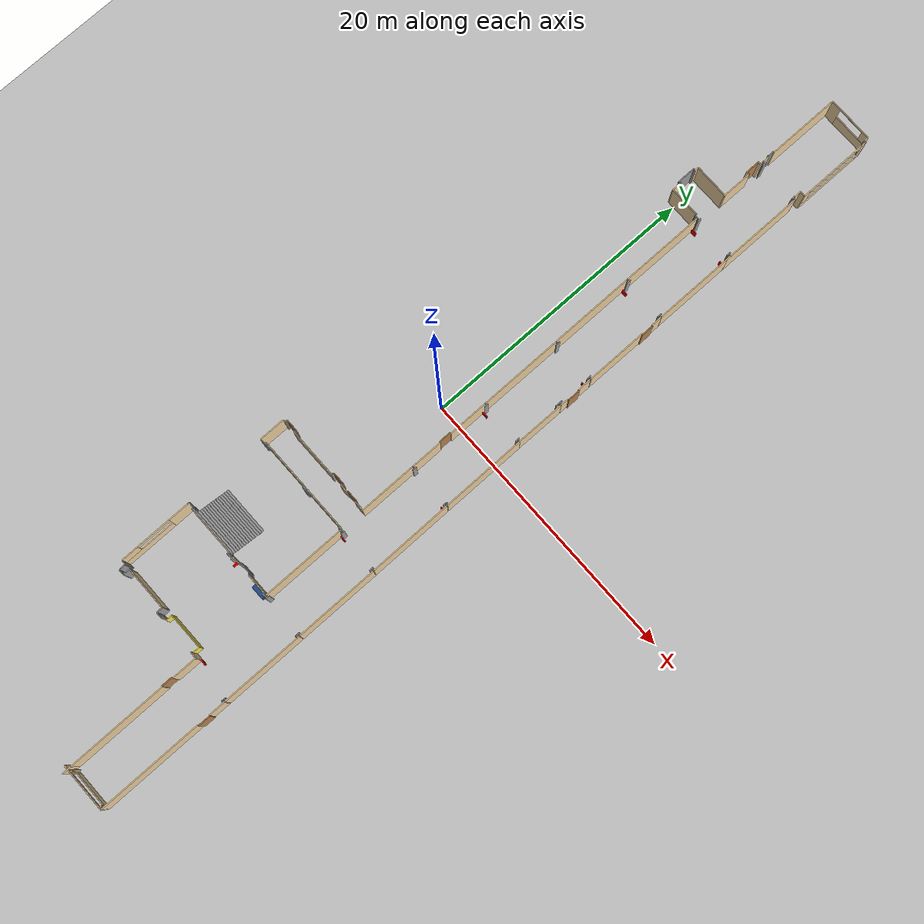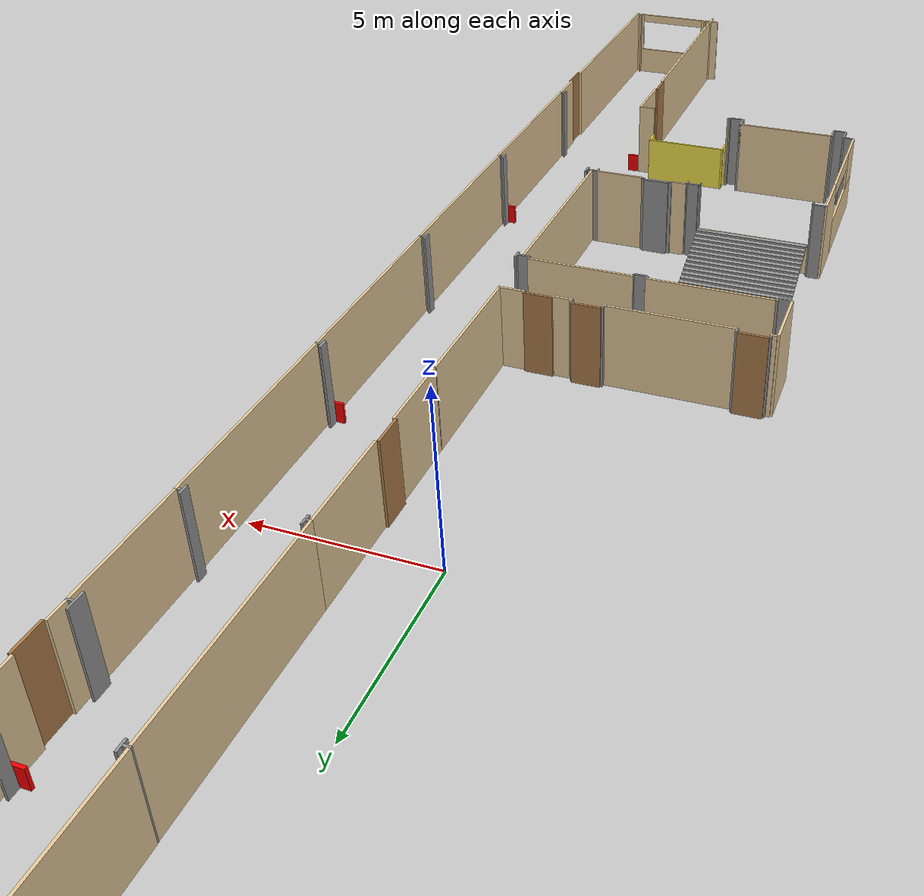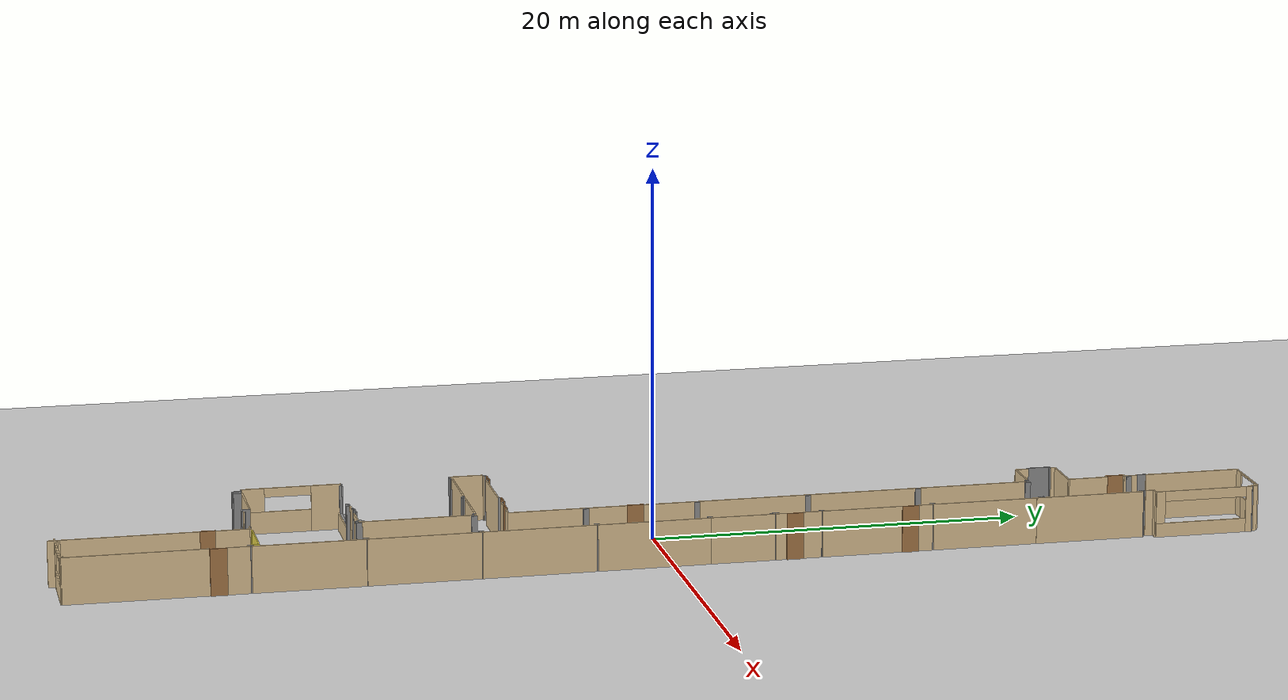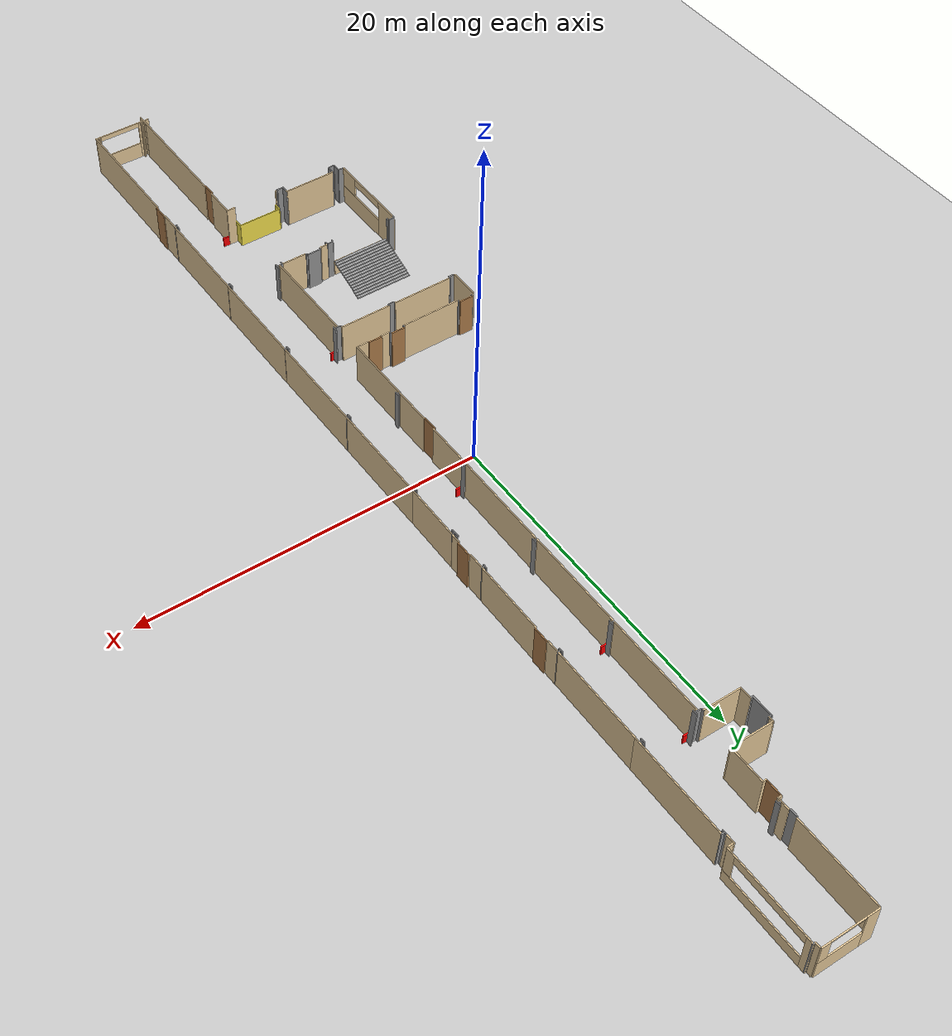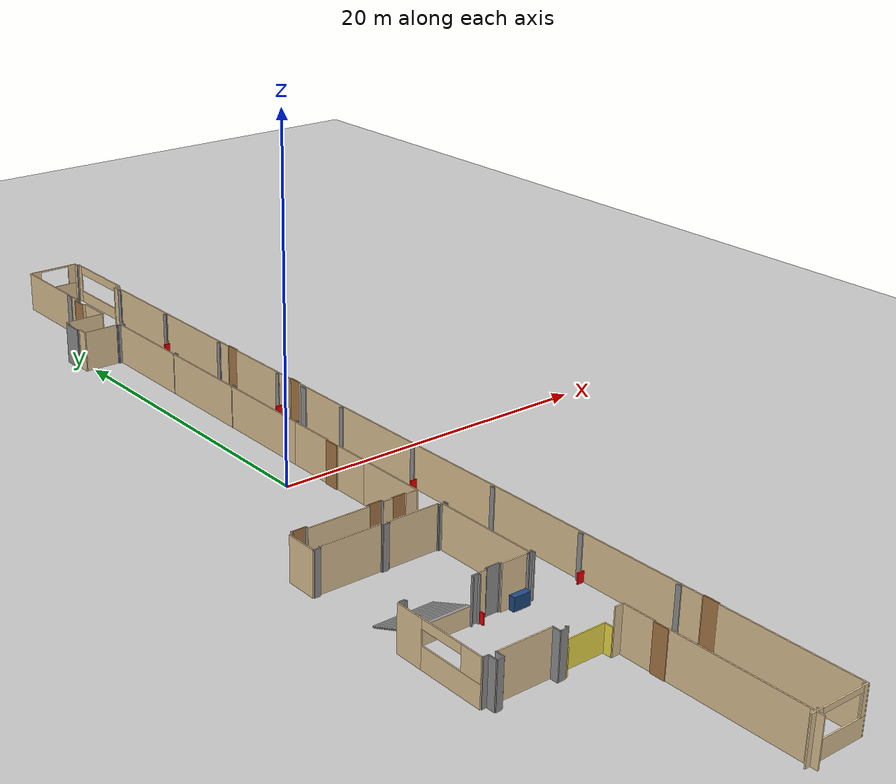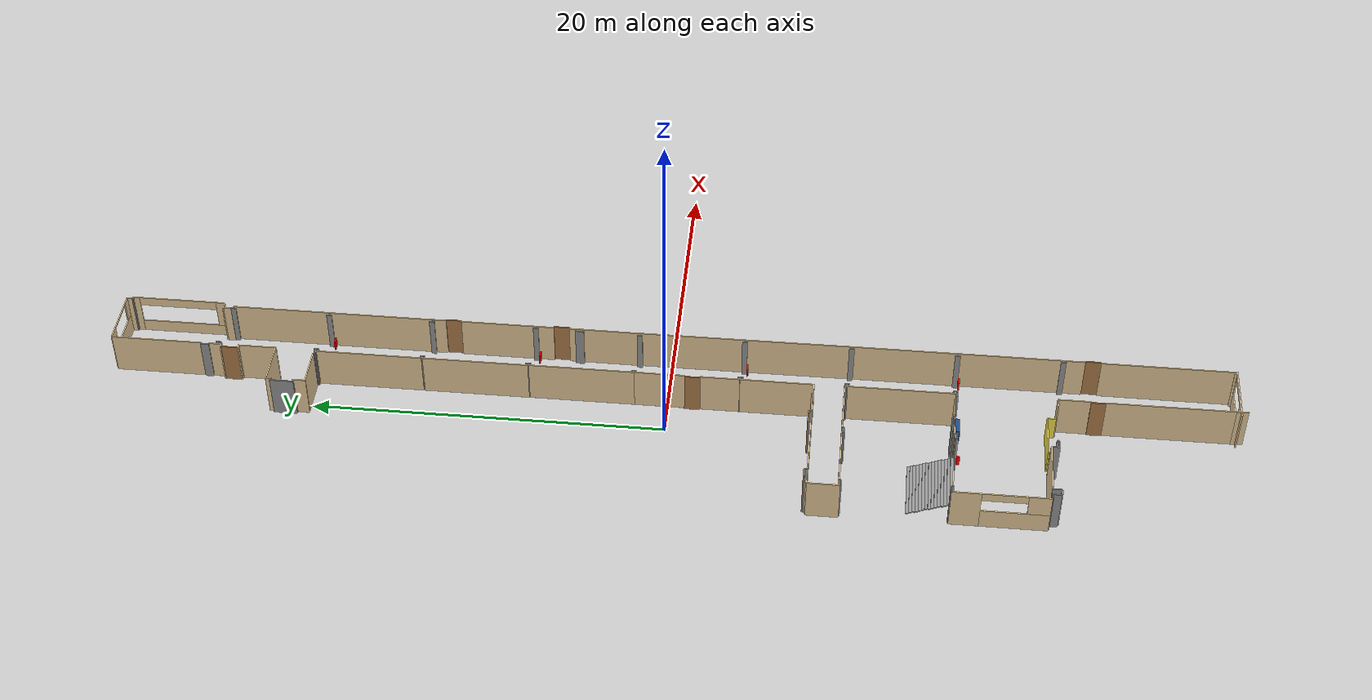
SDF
<sdf version="1.7">
 <world name="default">
  <light name="sun" type="directional">
   <pose>0 0 10 0 -0 0</pose>
   <diffuse>0.8 0.8 0.8 1</diffuse>
   <specular>0.2 0.2 0.2 1</specular>
   <attenuation>
    <range>1000</range>
    <constant>0.9</constant>
    <linear>0.01</linear>
    <quadratic>0.001</quadratic>
   </attenuation>
   <direction>-0.5 0.1 -0.9</direction>
   <spot><inner_angle>0</inner_angle><outer_angle>0</outer_angle><falloff>0</falloff></spot>
  </light>
  <model name="ground_plane">
   <static>1</static>
   <link name="link">
    <collision name="collision">
     <geometry><plane><normal>0 0 1</normal><size>100 100</size></plane></geometry>
     <surface>
      <contact><collide_bitmask>65535</collide_bitmask></contact>
      <friction><ode><mu>100</mu><mu2>50</mu2></ode></friction>
     </surface>
    </collision>
    <visual name="visual">
     <cast_shadows>0</cast_shadows>
     <geometry><plane><normal>0 0 1</normal><size>100 100</size></plane></geometry>
     <material>
      <script><uri>file://media/materials/scripts/gazebo.material</uri><name>Gazebo/Grey</name></script>
     </material>
    </visual>
   </link>
  </model>
  <gravity>0 0 -9.8</gravity>
  <magnetic_field>6e-06 2.3e-05 -4.2e-05</magnetic_field>
  <atmosphere type="adiabatic"/>
  <physics type="ode">
   <max_step_size>0.001</max_step_size>
   <real_time_factor>1</real_time_factor>
   <real_time_update_rate>1000</real_time_update_rate>
  </physics>
  <scene><ambient>0.4 0.4 0.4 1</ambient><background>0.7 0.7 0.7 1</background><shadows>1</shadows></scene>
  <spherical_coordinates>
   <surface_model>EARTH_WGS84</surface_model>
   <latitude_deg>0</latitude_deg>
   <longitude_deg>0</longitude_deg>
   <elevation>0</elevation>
   <heading_deg>0</heading_deg>
  </spherical_coordinates>
  <model name="Fakulte_koridor">
   <pose>-0.108629 -0.105707 0 0 -0 0</pose>
   <link name="Stairs_0">
    <visual name="Stairs_0_Visual_0">
     <pose>-3.19496 -13.5268 0.033333 0 -0 0</pose>
     <geometry><box><size>3.48995 0.166667 0.066667</size></box></geometry>
     <material>
      <script><uri>file://media/materials/scripts/gazebo.material</uri><name>Gazebo/Grey</name></script>
      <ambient>0.333333 0.341176 0.32549 1</ambient>
     </material>
     <meta><layer>0</layer></meta>
    </visual>
    <collision name="Stairs_0_Collision_0">
     <geometry><box><size>3.48995 0.166667 0.066667</size></box></geometry>
     <pose>-3.19496 -13.5268 0.033333 0 -0 0</pose>
    </collision>
    <visual name="Stairs_0_Visual_1">
     <pose>-3.19496 -13.6934 0.1 0 -0 0</pose>
     <geometry><box><size>3.48995 0.166667 0.066667</size></box></geometry>
     <material>
      <script><uri>file://media/materials/scripts/gazebo.material</uri><name>Gazebo/Grey</name></script>
      <ambient>0.333333 0.341176 0.32549 1</ambient>
     </material>
     <meta><layer>0</layer></meta>
    </visual>
    <collision name="Stairs_0_Collision_1">
     <geometry><box><size>3.48995 0.166667 0.066667</size></box></geometry>
     <pose>-3.19496 -13.6934 0.1 0 -0 0</pose>
    </collision>
    <visual name="Stairs_0_Visual_2">
     <pose>-3.19496 -13.8601 0.166667 0 -0 0</pose>
     <geometry><box><size>3.48995 0.166667 0.066667</size></box></geometry>
     <material>
      <script><uri>file://media/materials/scripts/gazebo.material</uri><name>Gazebo/Grey</name></script>
      <ambient>0.333333 0.341176 0.32549 1</ambient>
     </material>
     <meta><layer>0</layer></meta>
    </visual>
    <collision name="Stairs_0_Collision_2">
     <geometry><box><size>3.48995 0.166667 0.066667</size></box></geometry>
     <pose>-3.19496 -13.8601 0.166667 0 -0 0</pose>
    </collision>
    <visual name="Stairs_0_Visual_3">
     <pose>-3.19496 -14.0268 0.233333 0 -0 0</pose>
     <geometry><box><size>3.48995 0.166667 0.066667</size></box></geometry>
     <material>
      <script><uri>file://media/materials/scripts/gazebo.material</uri><name>Gazebo/Grey</name></script>
      <ambient>0.333333 0.341176 0.32549 1</ambient>
     </material>
     <meta><layer>0</layer></meta>
    </visual>
    <collision name="Stairs_0_Collision_3">
     <geometry><box><size>3.48995 0.166667 0.066667</size></box></geometry>
     <pose>-3.19496 -14.0268 0.233333 0 -0 0</pose>
    </collision>
    <visual name="Stairs_0_Visual_4">
     <pose>-3.19496 -14.1934 0.3 0 -0 0</pose>
     <geometry><box><size>3.48995 0.166667 0.066667</size></box></geometry>
     <material>
      <script><uri>file://media/materials/scripts/gazebo.material</uri><name>Gazebo/Grey</name></script>
      <ambient>0.333333 0.341176 0.32549 1</ambient>
     </material>
     <meta><layer>0</layer></meta>
    </visual>
    <collision name="Stairs_0_Collision_4">
     <geometry><box><size>3.48995 0.166667 0.066667</size></box></geometry>
     <pose>-3.19496 -14.1934 0.3 0 -0 0</pose>
    </collision>
    <visual name="Stairs_0_Visual_5">
     <pose>-3.19496 -14.3601 0.366667 0 -0 0</pose>
     <geometry><box><size>3.48995 0.166667 0.066667</size></box></geometry>
     <material>
      <script><uri>file://media/materials/scripts/gazebo.material</uri><name>Gazebo/Grey</name></script>
      <ambient>0.333333 0.341176 0.32549 1</ambient>
     </material>
     <meta><layer>0</layer></meta>
    </visual>
    <collision name="Stairs_0_Collision_5">
     <geometry><box><size>3.48995 0.166667 0.066667</size></box></geometry>
     <pose>-3.19496 -14.3601 0.366667 0 -0 0</pose>
    </collision>
    <visual name="Stairs_0_Visual_6">
     <pose>-3.19496 -14.5268 0.433333 0 -0 0</pose>
     <geometry><box><size>3.48995 0.166667 0.066667</size></box></geometry>
     <material>
      <script><uri>file://media/materials/scripts/gazebo.material</uri><name>Gazebo/Grey</name></script>
      <ambient>0.333333 0.341176 0.32549 1</ambient>
     </material>
     <meta><layer>0</layer></meta>
    </visual>
    <collision name="Stairs_0_Collision_6">
     <geometry><box><size>3.48995 0.166667 0.066667</size></box></geometry>
     <pose>-3.19496 -14.5268 0.433333 0 -0 0</pose>
    </collision>
    <visual name="Stairs_0_Visual_7">
     <pose>-3.19496 -14.6934 0.5 0 -0 0</pose>
     <geometry><box><size>3.48995 0.166667 0.066667</size></box></geometry>
     <material>
      <script><uri>file://media/materials/scripts/gazebo.material</uri><name>Gazebo/Grey</name></script>
      <ambient>0.333333 0.341176 0.32549 1</ambient>
     </material>
     <meta><layer>0</layer></meta>
    </visual>
    <collision name="Stairs_0_Collision_7">
     <geometry><box><size>3.48995 0.166667 0.066667</size></box></geometry>
     <pose>-3.19496 -14.6934 0.5 0 -0 0</pose>
    </collision>
    <visual name="Stairs_0_Visual_8">
     <pose>-3.19496 -14.8601 0.566667 0 -0 0</pose>
     <geometry><box><size>3.48995 0.166667 0.066667</size></box></geometry>
     <material>
      <script><uri>file://media/materials/scripts/gazebo.material</uri><name>Gazebo/Grey</name></script>
      <ambient>0.333333 0.341176 0.32549 1</ambient>
     </material>
     <meta><layer>0</layer></meta>
    </visual>
    <collision name="Stairs_0_Collision_8">
     <geometry><box><size>3.48995 0.166667 0.066667</size></box></geometry>
     <pose>-3.19496 -14.8601 0.566667 0 -0 0</pose>
    </collision>
    <visual name="Stairs_0_Visual_9">
     <pose>-3.19496 -15.0268 0.633333 0 -0 0</pose>
     <geometry><box><size>3.48995 0.166667 0.066667</size></box></geometry>
     <material>
      <script><uri>file://media/materials/scripts/gazebo.material</uri><name>Gazebo/Grey</name></script>
      <ambient>0.333333 0.341176 0.32549 1</ambient>
     </material>
     <meta><layer>0</layer></meta>
    </visual>
    <collision name="Stairs_0_Collision_9">
     <geometry><box><size>3.48995 0.166667 0.066667</size></box></geometry>
     <pose>-3.19496 -15.0268 0.633333 0 -0 0</pose>
    </collision>
    <visual name="Stairs_0_Visual_10">
     <pose>-3.19496 -15.1934 0.7 0 -0 0</pose>
     <geometry><box><size>3.48995 0.166667 0.066667</size></box></geometry>
     <material>
      <script><uri>file://media/materials/scripts/gazebo.material</uri><name>Gazebo/Grey</name></script>
      <ambient>0.333333 0.341176 0.32549 1</ambient>
     </material>
     <meta><layer>0</layer></meta>
    </visual>
    <collision name="Stairs_0_Collision_10">
     <geometry><box><size>3.48995 0.166667 0.066667</size></box></geometry>
     <pose>-3.19496 -15.1934 0.7 0 -0 0</pose>
    </collision>
    <visual name="Stairs_0_Visual_11">
     <pose>-3.19496 -15.3601 0.766667 0 -0 0</pose>
     <geometry><box><size>3.48995 0.166667 0.066667</size></box></geometry>
     <material>
      <script><uri>file://media/materials/scripts/gazebo.material</uri><name>Gazebo/Grey</name></script>
      <ambient>0.333333 0.341176 0.32549 1</ambient>
     </material>
     <meta><layer>0</layer></meta>
    </visual>
    <collision name="Stairs_0_Collision_11">
     <geometry><box><size>3.48995 0.166667 0.066667</size></box></geometry>
     <pose>-3.19496 -15.3601 0.766667 0 -0 0</pose>
    </collision>
    <visual name="Stairs_0_Visual_12">
     <pose>-3.19496 -15.5268 0.833333 0 -0 0</pose>
     <geometry><box><size>3.48995 0.166667 0.066667</size></box></geometry>
     <material>
      <script><uri>file://media/materials/scripts/gazebo.material</uri><name>Gazebo/Grey</name></script>
      <ambient>0.333333 0.341176 0.32549 1</ambient>
     </material>
     <meta><layer>0</layer></meta>
    </visual>
    <collision name="Stairs_0_Collision_12">
     <geometry><box><size>3.48995 0.166667 0.066667</size></box></geometry>
     <pose>-3.19496 -15.5268 0.833333 0 -0 0</pose>
    </collision>
    <visual name="Stairs_0_Visual_13">
     <pose>-3.19496 -15.6934 0.9 0 -0 0</pose>
     <geometry><box><size>3.48995 0.166667 0.066667</size></box></geometry>
     <material>
      <script><uri>file://media/materials/scripts/gazebo.material</uri><name>Gazebo/Grey</name></script>
      <ambient>0.333333 0.341176 0.32549 1</ambient>
     </material>
     <meta><layer>0</layer></meta>
    </visual>
    <collision name="Stairs_0_Collision_13">
     <geometry><box><size>3.48995 0.166667 0.066667</size></box></geometry>
     <pose>-3.19496 -15.6934 0.9 0 -0 0</pose>
    </collision>
    <visual name="Stairs_0_Visual_14">
     <pose>-3.19496 -15.8601 0.966667 0 -0 0</pose>
     <geometry><box><size>3.48995 0.166667 0.066667</size></box></geometry>
     <material>
      <script><uri>file://media/materials/scripts/gazebo.material</uri><name>Gazebo/Grey</name></script>
      <ambient>0.333333 0.341176 0.32549 1</ambient>
     </material>
     <meta><layer>0</layer></meta>
    </visual>
    <collision name="Stairs_0_Collision_14">
     <geometry><box><size>3.48995 0.166667 0.066667</size></box></geometry>
     <pose>-3.19496 -15.8601 0.966667 0 -0 0</pose>
    </collision>
   </link>
   <link name="Wall_100">
    <collision name="Wall_100_Collision">
     <geometry><box><size>0.3 0.06 2.5</size></box></geometry>
     <pose>0 0 1.25 0 -0 0</pose>
    </collision>
    <visual name="Wall_100_Visual">
     <pose>0 0 1.25 0 -0 0</pose>
     <geometry><box><size>0.3 0.06 2.5</size></box></geometry>
     <material>
      <script><uri>file://media/materials/scripts/gazebo.material</uri><name>Gazebo/Grey</name></script>
      <ambient>0.180392 0.203922 0.211765 1</ambient>
     </material>
     <meta><layer>0</layer></meta>
    </visual>
    <pose>5.11163 14.0287 0 0 -0 -1.5708</pose>
   </link>
   <link name="Wall_102">
    <collision name="Wall_102_Collision">
     <geometry><box><size>5.965 0.07 2.5</size></box></geometry>
     <pose>0 0 1.25 0 -0 0</pose>
    </collision>
    <visual name="Wall_102_Visual">
     <pose>0 0 1.25 0 -0 0</pose>
     <geometry><box><size>5.965 0.07 2.5</size></box></geometry>
     <material>
      <script><uri>file://media/materials/scripts/gazebo.material</uri><name>Gazebo/Grey</name></script>
      <ambient>0.921569 0.807843 0.615686 1</ambient>
     </material>
     <meta><layer>0</layer></meta>
    </visual>
    <pose>5.27021 17.0333 0 0 -0 -1.5708</pose>
   </link>
   <link name="Wall_104">
    <collision name="Wall_104_Collision">
     <geometry><box><size>0.175 0.06 2.5</size></box></geometry>
     <pose>0 0 1.25 0 -0 0</pose>
    </collision>
    <visual name="Wall_104_Visual">
     <pose>0 0 1.25 0 -0 0</pose>
     <geometry><box><size>0.175 0.06 2.5</size></box></geometry>
     <material>
      <script><uri>file://media/materials/scripts/gazebo.material</uri><name>Gazebo/Grey</name></script>
      <ambient>0.180392 0.203922 0.211765 1</ambient>
     </material>
     <meta><layer>0</layer></meta>
    </visual>
    <pose>5.21005 19.996 0 0 -0 0</pose>
   </link>
   <link name="Wall_106">
    <collision name="Wall_106_Collision">
     <geometry><box><size>0.3 0.06 2.5</size></box></geometry>
     <pose>0 0 1.25 0 -0 0</pose>
    </collision>
    <visual name="Wall_106_Visual">
     <pose>0 0 1.25 0 -0 0</pose>
     <geometry><box><size>0.3 0.06 2.5</size></box></geometry>
     <material>
      <script><uri>file://media/materials/scripts/gazebo.material</uri><name>Gazebo/Grey</name></script>
      <ambient>0.180392 0.203922 0.211765 1</ambient>
     </material>
     <meta><layer>0</layer></meta>
    </visual>
    <pose>5.08827 20.0046 0 0 -0 -1.5708</pose>
   </link>
   <link name="Wall_108">
    <collision name="Wall_108_Collision">
     <geometry><box><size>5.895 0.07 2.5</size></box></geometry>
     <pose>0 0 1.25 0 -0 0</pose>
    </collision>
    <visual name="Wall_108_Visual">
     <pose>0 0 1.25 0 -0 0</pose>
     <geometry><box><size>5.895 0.07 2.5</size></box></geometry>
     <material>
      <script><uri>file://media/materials/scripts/gazebo.material</uri><name>Gazebo/Grey</name></script>
      <ambient>0.921569 0.807843 0.615686 1</ambient>
     </material>
     <meta><layer>0</layer></meta>
    </visual>
    <pose>5.27802 22.6416 0 0 -0 -1.5708</pose>
   </link>
   <link name="Wall_110">
    <collision name="Wall_110_Collision">
     <geometry><box><size>0.175 0.06 2.5</size></box></geometry>
     <pose>0 0 1.25 0 -0 0</pose>
    </collision>
    <visual name="Wall_110_Visual">
     <pose>0 0 1.25 0 -0 0</pose>
     <geometry><box><size>0.175 0.06 2.5</size></box></geometry>
     <material>
      <script><uri>file://media/materials/scripts/gazebo.material</uri><name>Gazebo/Grey</name></script>
      <ambient>0.180392 0.203922 0.211765 1</ambient>
     </material>
     <meta><layer>0</layer></meta>
    </visual>
    <pose>5.21975 25.6028 0 0 -0 0</pose>
   </link>
   <link name="Wall_112">
    <collision name="Wall_112_Collision">
     <geometry><box><size>0.3 0.06 2.5</size></box></geometry>
     <pose>0 0 1.25 0 -0 0</pose>
    </collision>
    <visual name="Wall_112_Visual">
     <pose>0 0 1.25 0 -0 0</pose>
     <geometry><box><size>0.3 0.06 2.5</size></box></geometry>
     <material>
      <script><uri>file://media/materials/scripts/gazebo.material</uri><name>Gazebo/Grey</name></script>
      <ambient>0.180392 0.203922 0.211765 1</ambient>
     </material>
     <meta><layer>0</layer></meta>
    </visual>
    <pose>5.11751 25.6043 0 0 -0 -1.5708</pose>
   </link>
   <link name="Wall_114">
    <collision name="Wall_114_Collision">
     <geometry><box><size>0.505 0.07 2.5</size></box></geometry>
     <pose>0 0 1.25 0 -0 0</pose>
    </collision>
    <visual name="Wall_114_Visual">
     <pose>0 0 1.25 0 -0 0</pose>
     <geometry><box><size>0.505 0.07 2.5</size></box></geometry>
     <material>
      <script><uri>file://media/materials/scripts/gazebo.material</uri><name>Gazebo/Grey</name></script>
      <ambient>0.921569 0.807843 0.615686 1</ambient>
     </material>
     <meta><layer>0</layer></meta>
    </visual>
    <pose>5.1239 26.0091 0 0 -0 -1.5708</pose>
   </link>
   <link name="Wall_118">
    <collision name="Wall_118_Collision">
     <geometry><box><size>0.4 0.07 2.5</size></box></geometry>
     <pose>0 0 1.25 0 -0 0</pose>
    </collision>
    <visual name="Wall_118_Visual">
     <pose>0 0 1.25 0 -0 0</pose>
     <geometry><box><size>0.4 0.07 2.5</size></box></geometry>
     <material>
      <script><uri>file://media/materials/scripts/gazebo.material</uri><name>Gazebo/Grey</name></script>
      <ambient>0.921569 0.807843 0.615686 1</ambient>
     </material>
     <meta><layer>0</layer></meta>
    </visual>
    <pose>5.28591 26.2172 0 0 -0 0</pose>
   </link>
   <link name="Wall_120">
    <pose>5.5144 28.9535 0 0 -0 -1.5708</pose>
    <visual name="Wall_120_Visual_0">
     <pose>-2.49861 0 1.25 0 -0 0</pose>
     <geometry><box><size>0.407786 0.07 2.5</size></box></geometry>
     <material>
      <script><uri>file://media/materials/scripts/gazebo.material</uri><name>Gazebo/Grey</name></script>
      <ambient>0.921569 0.807843 0.615686 1</ambient>
     </material>
     <meta><layer>0</layer></meta>
    </visual>
    <collision name="Wall_120_Collision_0">
     <geometry><box><size>0.407786 0.07 2.5</size></box></geometry>
     <pose>-2.49861 0 1.25 0 -0 0</pose>
    </collision>
    <visual name="Wall_120_Visual_1">
     <pose>0.203893 0 0.375 0 -0 0</pose>
     <geometry><box><size>4.99721 0.07 0.75</size></box></geometry>
     <material>
      <script><uri>file://media/materials/scripts/gazebo.material</uri><name>Gazebo/Grey</name></script>
      <ambient>0.921569 0.807843 0.615686 1</ambient>
     </material>
     <meta><layer>0</layer></meta>
    </visual>
    <collision name="Wall_120_Collision_1">
     <geometry><box><size>4.99721 0.07 0.75</size></box></geometry>
     <pose>0.203893 0 0.375 0 -0 0</pose>
    </collision>
    <visual name="Wall_120_Visual_2">
     <pose>2.45389 0 1.625 0 -0 0</pose>
     <geometry><box><size>0.497214 0.07 1.75</size></box></geometry>
     <material>
      <script><uri>file://media/materials/scripts/gazebo.material</uri><name>Gazebo/Grey</name></script>
      <ambient>0.921569 0.807843 0.615686 1</ambient>
     </material>
     <meta><layer>0</layer></meta>
    </visual>
    <collision name="Wall_120_Collision_2">
     <geometry><box><size>0.497214 0.07 1.75</size></box></geometry>
     <pose>2.45389 0 1.625 0 -0 0</pose>
    </collision>
    <visual name="Wall_120_Visual_3">
     <pose>-0.044714 0 2.225 0 -0 0</pose>
     <geometry><box><size>4.5 0.07 0.55</size></box></geometry>
     <material>
      <script><uri>file://media/materials/scripts/gazebo.material</uri><name>Gazebo/Grey</name></script>
      <ambient>0.921569 0.807843 0.615686 1</ambient>
     </material>
     <meta><layer>0</layer></meta>
    </visual>
    <collision name="Wall_120_Collision_3">
     <geometry><box><size>4.5 0.07 0.55</size></box></geometry>
     <pose>-0.044714 0 2.225 0 -0 0</pose>
    </collision>
   </link>
   <link name="Wall_122">
    <collision name="Wall_122_Collision">
     <geometry><box><size>0.195 0.07 2.5</size></box></geometry>
     <pose>0 0 1.25 0 -0 0</pose>
    </collision>
    <visual name="Wall_122_Visual">
     <pose>0 0 1.25 0 -0 0</pose>
     <geometry><box><size>0.195 0.07 2.5</size></box></geometry>
     <material>
      <script><uri>file://media/materials/scripts/gazebo.material</uri><name>Gazebo/Grey</name></script>
      <ambient>1 1 1 1</ambient>
     </material>
     <meta><layer>0</layer></meta>
    </visual>
    <pose>5.4612 31.621 0 0 -0 0</pose>
   </link>
   <link name="Wall_124">
    <collision name="Wall_124_Collision">
     <geometry><box><size>0.32 0.07 2.5</size></box></geometry>
     <pose>0 0 1.25 0 -0 0</pose>
    </collision>
    <visual name="Wall_124_Visual">
     <pose>0 0 1.25 0 -0 0</pose>
     <geometry><box><size>0.32 0.07 2.5</size></box></geometry>
     <material>
      <script><uri>file://media/materials/scripts/gazebo.material</uri><name>Gazebo/Grey</name></script>
      <ambient>0.921569 0.807843 0.615686 1</ambient>
     </material>
     <meta><layer>0</layer></meta>
    </visual>
    <pose>5.40314 31.7556 0 0 -0 -1.5708</pose>
   </link>
   <link name="Wall_126">
    <pose>3.74779 31.9519 0 0 -0 0</pose>
    <visual name="Wall_126_Visual_0">
     <pose>-1.26795 0 1.25 0 -0 0</pose>
     <geometry><box><size>0.743101 0.07 2.5</size></box></geometry>
     <material>
      <script><uri>file://media/materials/scripts/gazebo.material</uri><name>Gazebo/Grey</name></script>
      <ambient>0.921569 0.807843 0.615686 1</ambient>
     </material>
     <meta><layer>0</layer></meta>
    </visual>
    <collision name="Wall_126_Collision_0">
     <geometry><box><size>0.743101 0.07 2.5</size></box></geometry>
     <pose>-1.26795 0 1.25 0 -0 0</pose>
    </collision>
    <visual name="Wall_126_Visual_1">
     <pose>0.37155 0 0.6 0 -0 0</pose>
     <geometry><box><size>2.5359 0.07 1.2</size></box></geometry>
     <material>
      <script><uri>file://media/materials/scripts/gazebo.material</uri><name>Gazebo/Grey</name></script>
      <ambient>0.921569 0.807843 0.615686 1</ambient>
     </material>
     <meta><layer>0</layer></meta>
    </visual>
    <collision name="Wall_126_Collision_1">
     <geometry><box><size>2.5359 0.07 1.2</size></box></geometry>
     <pose>0.37155 0 0.6 0 -0 0</pose>
    </collision>
    <visual name="Wall_126_Visual_2">
     <pose>1.37155 0 1.85 0 -0 0</pose>
     <geometry><box><size>0.535899 0.07 1.3</size></box></geometry>
     <material>
      <script><uri>file://media/materials/scripts/gazebo.material</uri><name>Gazebo/Grey</name></script>
      <ambient>0.921569 0.807843 0.615686 1</ambient>
     </material>
     <meta><layer>0</layer></meta>
    </visual>
    <collision name="Wall_126_Collision_2">
     <geometry><box><size>0.535899 0.07 1.3</size></box></geometry>
     <pose>1.37155 0 1.85 0 -0 0</pose>
    </collision>
    <visual name="Wall_126_Visual_3">
     <pose>0.103601 0 2.45 0 -0 0</pose>
     <geometry><box><size>2 0.07 0.1</size></box></geometry>
     <material>
      <script><uri>file://media/materials/scripts/gazebo.material</uri><name>Gazebo/Grey</name></script>
      <ambient>0.921569 0.807843 0.615686 1</ambient>
     </material>
     <meta><layer>0</layer></meta>
    </visual>
    <collision name="Wall_126_Collision_3">
     <geometry><box><size>2 0.07 0.1</size></box></geometry>
     <pose>0.103601 0 2.45 0 -0 0</pose>
    </collision>
   </link>
   <link name="Wall_128">
    <collision name="Wall_128_Collision">
     <geometry><box><size>5.145 0.07 2.5</size></box></geometry>
     <pose>0 0 1.25 0 -0 0</pose>
    </collision>
    <visual name="Wall_128_Visual">
     <pose>0 0 1.25 0 -0 0</pose>
     <geometry><box><size>5.145 0.07 2.5</size></box></geometry>
     <material>
      <script><uri>file://media/materials/scripts/gazebo.material</uri><name>Gazebo/Grey</name></script>
      <ambient>0.921569 0.807843 0.615686 1</ambient>
     </material>
     <meta><layer>0</layer></meta>
    </visual>
    <pose>2.09688 29.3576 0 0 -0 -1.5708</pose>
   </link>
   <link name="Wall_130">
    <collision name="Wall_130_Collision">
     <geometry><box><size>0.495 0.07 2.5</size></box></geometry>
     <pose>0 0 1.25 0 -0 0</pose>
    </collision>
    <visual name="Wall_130_Visual">
     <pose>0 0 1.25 0 -0 0</pose>
     <geometry><box><size>0.495 0.07 2.5</size></box></geometry>
     <material>
      <script><uri>file://media/materials/scripts/gazebo.material</uri><name>Gazebo/Grey</name></script>
      <ambient>0.729412 0.741176 0.713726 1</ambient>
     </material>
     <meta><layer>0</layer></meta>
    </visual>
    <pose>2.03085 26.5424 0 0 -0 -1.5708</pose>
   </link>
   <link name="Wall_132">
    <collision name="Wall_132_Collision">
     <geometry><box><size>0.745 0.07 2.5</size></box></geometry>
     <pose>0 0 1.25 0 -0 0</pose>
    </collision>
    <visual name="Wall_132_Visual">
     <pose>0 0 1.25 0 -0 0</pose>
     <geometry><box><size>0.745 0.07 2.5</size></box></geometry>
     <material>
      <script><uri>file://media/materials/scripts/gazebo.material</uri><name>Gazebo/Grey</name></script>
      <ambient>0.921569 0.807843 0.615686 1</ambient>
     </material>
     <meta><layer>0</layer></meta>
    </visual>
    <pose>2.09827 25.9291 0 0 -0 -1.5708</pose>
   </link>
   <link name="Wall_134">
    <collision name="Wall_134_Collision">
     <geometry><box><size>0.175 0.06 2.5</size></box></geometry>
     <pose>0 0 1.25 0 -0 0</pose>
    </collision>
    <visual name="Wall_134_Visual">
     <pose>0 0 1.25 0 -0 0</pose>
     <geometry><box><size>0.175 0.06 2.5</size></box></geometry>
     <material>
      <script><uri>file://media/materials/scripts/gazebo.material</uri><name>Gazebo/Grey</name></script>
      <ambient>0.180392 0.203922 0.211765 1</ambient>
     </material>
     <meta><layer>0</layer></meta>
    </visual>
    <pose>2.15167 25.7938 0 0 -0 0</pose>
   </link>
   <link name="Wall_136">
    <collision name="Wall_136_Collision">
     <geometry><box><size>0.3 0.06 2.5</size></box></geometry>
     <pose>0 0 1.25 0 -0 0</pose>
    </collision>
    <visual name="Wall_136_Visual">
     <pose>0 0 1.25 0 -0 0</pose>
     <geometry><box><size>0.3 0.06 2.5</size></box></geometry>
     <material>
      <script><uri>file://media/materials/scripts/gazebo.material</uri><name>Gazebo/Grey</name></script>
      <ambient>0.180392 0.203922 0.211765 1</ambient>
     </material>
     <meta><layer>0</layer></meta>
    </visual>
    <pose>2.268 25.7827 0 0 -0 -1.5708</pose>
   </link>
   <link name="Wall_138">
    <collision name="Wall_138_Collision">
     <geometry><box><size>0.262 0.07 2.5</size></box></geometry>
     <pose>0 0 1.25 0 -0 0</pose>
    </collision>
    <visual name="Wall_138_Visual">
     <pose>0 0 1.25 0 -0 0</pose>
     <geometry><box><size>0.262 0.07 2.5</size></box></geometry>
     <material>
      <script><uri>file://media/materials/scripts/gazebo.material</uri><name>Gazebo/Grey</name></script>
      <ambient>0.921569 0.807843 0.615686 1</ambient>
     </material>
     <meta><layer>0</layer></meta>
    </visual>
    <pose>2.00137 25.5882 0 0 -0 3.14159</pose>
   </link>
   <link name="Wall_140">
    <collision name="Wall_140_Collision">
     <geometry><box><size>0.933 0.07 2.5</size></box></geometry>
     <pose>0 0 1.25 0 -0 0</pose>
    </collision>
    <visual name="Wall_140_Visual">
     <pose>0 0 1.25 0 -0 0</pose>
     <geometry><box><size>0.933 0.07 2.5</size></box></geometry>
     <material>
      <script><uri>file://media/materials/scripts/gazebo.material</uri><name>Gazebo/Wood</name></script>
      <ambient>1 1 1 1</ambient>
     </material>
     <meta><layer>0</layer></meta>
    </visual>
    <pose>1.90607 25.0907 0 0 -0 -1.5708</pose>
   </link>
   <link name="Wall_142">
    <collision name="Wall_142_Collision">
     <geometry><box><size>0.262 0.07 2.5</size></box></geometry>
     <pose>0 0 1.25 0 -0 0</pose>
    </collision>
    <visual name="Wall_142_Visual">
     <pose>0 0 1.25 0 -0 0</pose>
     <geometry><box><size>0.262 0.07 2.5</size></box></geometry>
     <material>
      <script><uri>file://media/materials/scripts/gazebo.material</uri><name>Gazebo/Grey</name></script>
      <ambient>0.921569 0.807843 0.615686 1</ambient>
     </material>
     <meta><layer>0</layer></meta>
    </visual>
    <pose>2.00059 24.593 0 0 -0 0</pose>
   </link>
   <link name="Wall_144">
    <collision name="Wall_144_Collision">
     <geometry><box><size>2.203 0.07 2.5</size></box></geometry>
     <pose>0 0 1.25 0 -0 0</pose>
    </collision>
    <visual name="Wall_144_Visual">
     <pose>0 0 1.25 0 -0 0</pose>
     <geometry><box><size>2.203 0.07 2.5</size></box></geometry>
     <material>
      <script><uri>file://media/materials/scripts/gazebo.material</uri><name>Gazebo/Grey</name></script>
      <ambient>0.921569 0.807843 0.615686 1</ambient>
     </material>
     <meta><layer>0</layer></meta>
    </visual>
    <pose>2.09965 23.523 0 0 -0 -1.5708</pose>
   </link>
   <link name="Wall_146">
    <collision name="Wall_146_Collision">
     <geometry><box><size>2.483 0.07 2.5</size></box></geometry>
     <pose>0 0 1.25 0 -0 0</pose>
    </collision>
    <visual name="Wall_146_Visual">
     <pose>0 0 1.25 0 -0 0</pose>
     <geometry><box><size>2.483 0.07 2.5</size></box></geometry>
     <material>
      <script><uri>file://media/materials/scripts/gazebo.material</uri><name>Gazebo/Grey</name></script>
      <ambient>0.921569 0.807843 0.615686 1</ambient>
     </material>
     <meta><layer>0</layer></meta>
    </visual>
    <pose>0.894313 22.4573 0 0 -0 0</pose>
   </link>
   <link name="Wall_148">
    <collision name="Wall_148_Collision">
     <geometry><box><size>0.345 0.07 2.5</size></box></geometry>
     <pose>0 0 1.25 0 -0 0</pose>
    </collision>
    <visual name="Wall_148_Visual">
     <pose>0 0 1.25 0 -0 0</pose>
     <geometry><box><size>0.345 0.07 2.5</size></box></geometry>
     <material>
      <script><uri>file://media/materials/scripts/gazebo.material</uri><name>Gazebo/Grey</name></script>
      <ambient>0.921569 0.807843 0.615686 1</ambient>
     </material>
     <meta><layer>0</layer></meta>
    </visual>
    <pose>-0.377773 22.3219 0 0 -0 -1.5708</pose>
   </link>
   <link name="Wall_150">
    <collision name="Wall_150_Collision">
     <geometry><box><size>0.153 0.07 2.5</size></box></geometry>
     <pose>0 0 1.25 0 -0 0</pose>
    </collision>
    <visual name="Wall_150_Visual">
     <pose>0 0 1.25 0 -0 0</pose>
     <geometry><box><size>0.153 0.07 2.5</size></box></geometry>
     <material>
      <script><uri>file://media/materials/scripts/gazebo.material</uri><name>Gazebo/Grey</name></script>
      <ambient>0.533333 0.541176 0.521569 1</ambient>
     </material>
     <meta><layer>0</layer></meta>
    </visual>
    <pose>-0.413524 22.1834 0 0 -0 3.14159</pose>
   </link>
   <link name="Wall_152">
    <collision name="Wall_152_Collision">
     <geometry><box><size>1.338 0.07 2.5</size></box></geometry>
     <pose>0 0 1.25 0 -0 0</pose>
    </collision>
    <visual name="Wall_152_Visual">
     <pose>0 0 1.25 0 -0 0</pose>
     <geometry><box><size>1.338 0.07 2.5</size></box></geometry>
     <material>
      <script><uri>file://media/materials/scripts/gazebo.material</uri><name>Gazebo/Grey</name></script>
      <ambient>0.533333 0.541176 0.521569 1</ambient>
     </material>
     <meta><layer>0</layer></meta>
    </visual>
    <pose>-0.516682 21.5521 0 0 -0 -1.5708</pose>
   </link>
   <link name="Wall_154">
    <collision name="Wall_154_Collision">
     <geometry><box><size>0.153 0.07 2.5</size></box></geometry>
     <pose>0 0 1.25 0 -0 0</pose>
    </collision>
    <visual name="Wall_154_Visual">
     <pose>0 0 1.25 0 -0 0</pose>
     <geometry><box><size>0.153 0.07 2.5</size></box></geometry>
     <material>
      <script><uri>file://media/materials/scripts/gazebo.material</uri><name>Gazebo/Grey</name></script>
      <ambient>0.533333 0.541176 0.521569 1</ambient>
     </material>
     <meta><layer>0</layer></meta>
    </visual>
    <pose>-0.421701 20.9154 0 0 -0 0</pose>
   </link>
   <link name="Wall_156">
    <collision name="Wall_156_Collision">
     <geometry><box><size>0.738 0.07 2.5</size></box></geometry>
     <pose>0 0 1.25 0 -0 0</pose>
    </collision>
    <visual name="Wall_156_Visual">
     <pose>0 0 1.25 0 -0 0</pose>
     <geometry><box><size>0.738 0.07 2.5</size></box></geometry>
     <material>
      <script><uri>file://media/materials/scripts/gazebo.material</uri><name>Gazebo/Grey</name></script>
      <ambient>0.921569 0.807843 0.615686 1</ambient>
     </material>
     <meta><layer>0</layer></meta>
    </visual>
    <pose>-0.371379 20.5814 0 0 -0 -1.5708</pose>
   </link>
   <link name="Wall_158">
    <collision name="Wall_158_Collision">
     <geometry><box><size>2.19 0.07 2.5</size></box></geometry>
     <pose>0 0 1.25 0 -0 0</pose>
    </collision>
    <visual name="Wall_158_Visual">
     <pose>0 0 1.25 0 -0 0</pose>
     <geometry><box><size>2.19 0.07 2.5</size></box></geometry>
     <material>
      <script><uri>file://media/materials/scripts/gazebo.material</uri><name>Gazebo/Grey</name></script>
      <ambient>0.921569 0.807843 0.615686 1</ambient>
     </material>
     <meta><layer>0</layer></meta>
    </visual>
    <pose>0.740321 20.2486 0 0 -0 0</pose>
   </link>
   <link name="Wall_160">
    <collision name="Wall_160_Collision">
     <geometry><box><size>0.13 0.06 2.5</size></box></geometry>
     <pose>0 0 1.25 0 -0 0</pose>
    </collision>
    <visual name="Wall_160_Visual">
     <pose>0 0 1.25 0 -0 0</pose>
     <geometry><box><size>0.13 0.06 2.5</size></box></geometry>
     <material>
      <script><uri>file://media/materials/scripts/gazebo.material</uri><name>Gazebo/Grey</name></script>
      <ambient>0.180392 0.203922 0.211765 1</ambient>
     </material>
     <meta><layer>0</layer></meta>
    </visual>
    <pose>1.81046 20.2205 0 0 -0 -1.5708</pose>
   </link>
   <link name="Wall_162">
    <collision name="Wall_162_Collision">
     <geometry><box><size>0.35 0.06 2.5</size></box></geometry>
     <pose>0 0 1.25 0 -0 0</pose>
    </collision>
    <visual name="Wall_162_Visual">
     <pose>0 0 1.25 0 -0 0</pose>
     <geometry><box><size>0.35 0.06 2.5</size></box></geometry>
     <material>
      <script><uri>file://media/materials/scripts/gazebo.material</uri><name>Gazebo/Grey</name></script>
      <ambient>0.180392 0.203922 0.211765 1</ambient>
     </material>
     <meta><layer>0</layer></meta>
    </visual>
    <pose>2.01991 20.1265 0 0 -0 0</pose>
   </link>
   <link name="Wall_164">
    <collision name="Wall_164_Collision">
     <geometry><box><size>0.3 0.06 2.5</size></box></geometry>
     <pose>0 0 1.25 0 -0 0</pose>
    </collision>
    <visual name="Wall_164_Visual">
     <pose>0 0 1.25 0 -0 0</pose>
     <geometry><box><size>0.3 0.06 2.5</size></box></geometry>
     <material>
      <script><uri>file://media/materials/scripts/gazebo.material</uri><name>Gazebo/Grey</name></script>
      <ambient>0.180392 0.203922 0.211765 1</ambient>
     </material>
     <meta><layer>0</layer></meta>
    </visual>
    <pose>2.22081 20.1358 0 0 -0 -1.5708</pose>
   </link>
   <link name="Wall_166">
    <collision name="Wall_166_Collision">
     <geometry><box><size>5.995 0.07 2.5</size></box></geometry>
     <pose>0 0 1.25 0 -0 0</pose>
    </collision>
    <visual name="Wall_166_Visual">
     <pose>0 0 1.25 0 -0 0</pose>
     <geometry><box><size>5.995 0.07 2.5</size></box></geometry>
     <material>
      <script><uri>file://media/materials/scripts/gazebo.material</uri><name>Gazebo/Grey</name></script>
      <ambient>0.921569 0.807843 0.615686 1</ambient>
     </material>
     <meta><layer>0</layer></meta>
    </visual>
    <pose>2.04763 17.0972 0 0 -0 -1.5708</pose>
   </link>
   <link name="Wall_168">
    <collision name="Wall_168_Collision">
     <geometry><box><size>0.175 0.06 2.5</size></box></geometry>
     <pose>0 0 1.25 0 -0 0</pose>
    </collision>
    <visual name="Wall_168_Visual">
     <pose>0 0 1.25 0 -0 0</pose>
     <geometry><box><size>0.175 0.06 2.5</size></box></geometry>
     <material>
      <script><uri>file://media/materials/scripts/gazebo.material</uri><name>Gazebo/Grey</name></script>
      <ambient>0.180392 0.203922 0.211765 1</ambient>
     </material>
     <meta><layer>0</layer></meta>
    </visual>
    <pose>2.10611 14.0679 0 0 -0 0</pose>
   </link>
   <link name="Wall_170">
    <collision name="Wall_170_Collision">
     <geometry><box><size>0.3 0.06 2.5</size></box></geometry>
     <pose>0 0 1.25 0 -0 0</pose>
    </collision>
    <visual name="Wall_170_Visual">
     <pose>0 0 1.25 0 -0 0</pose>
     <geometry><box><size>0.3 0.06 2.5</size></box></geometry>
     <material>
      <script><uri>file://media/materials/scripts/gazebo.material</uri><name>Gazebo/Grey</name></script>
      <ambient>0.180392 0.203922 0.211765 1</ambient>
     </material>
     <meta><layer>0</layer></meta>
    </visual>
    <pose>2.20124 14.0542 0 0 -0 -1.5708</pose>
   </link>
   <link name="Wall_172">
    <collision name="Wall_172_Collision">
     <geometry><box><size>5.995 0.07 2.5</size></box></geometry>
     <pose>0 0 1.25 0 -0 0</pose>
    </collision>
    <visual name="Wall_172_Visual">
     <pose>0 0 1.25 0 -0 0</pose>
     <geometry><box><size>5.995 0.07 2.5</size></box></geometry>
     <material>
      <script><uri>file://media/materials/scripts/gazebo.material</uri><name>Gazebo/Grey</name></script>
      <ambient>0.921569 0.807843 0.615686 1</ambient>
     </material>
     <meta><layer>0</layer></meta>
    </visual>
    <pose>2.04763 11.0372 0 0 -0 -1.5708</pose>
   </link>
   <link name="Wall_174">
    <collision name="Wall_174_Collision">
     <geometry><box><size>0.175 0.06 2.5</size></box></geometry>
     <pose>0 0 1.25 0 -0 0</pose>
    </collision>
    <visual name="Wall_174_Visual">
     <pose>0 0 1.25 0 -0 0</pose>
     <geometry><box><size>0.175 0.06 2.5</size></box></geometry>
     <material>
      <script><uri>file://media/materials/scripts/gazebo.material</uri><name>Gazebo/Grey</name></script>
      <ambient>0.180392 0.203922 0.211765 1</ambient>
     </material>
     <meta><layer>0</layer></meta>
    </visual>
    <pose>2.10606 8.02576 0 0 -0 0</pose>
   </link>
   <link name="Wall_176">
    <collision name="Wall_176_Collision">
     <geometry><box><size>0.3 0.06 2.5</size></box></geometry>
     <pose>0 0 1.25 0 -0 0</pose>
    </collision>
    <visual name="Wall_176_Visual">
     <pose>0 0 1.25 0 -0 0</pose>
     <geometry><box><size>0.3 0.06 2.5</size></box></geometry>
     <material>
      <script><uri>file://media/materials/scripts/gazebo.material</uri><name>Gazebo/Grey</name></script>
      <ambient>0.180392 0.203922 0.211765 1</ambient>
     </material>
     <meta><layer>0</layer></meta>
    </visual>
    <pose>2.2092 8.04168 0 0 -0 -1.5708</pose>
   </link>
   <link name="Wall_178">
    <collision name="Wall_178_Collision">
     <geometry><box><size>5.995 0.07 2.5</size></box></geometry>
     <pose>0 0 1.25 0 -0 0</pose>
    </collision>
    <visual name="Wall_178_Visual">
     <pose>0 0 1.25 0 -0 0</pose>
     <geometry><box><size>5.995 0.07 2.5</size></box></geometry>
     <material>
      <script><uri>file://media/materials/scripts/gazebo.material</uri><name>Gazebo/Grey</name></script>
      <ambient>0.921569 0.807843 0.615686 1</ambient>
     </material>
     <meta><layer>0</layer></meta>
    </visual>
    <pose>2.05863 5.00721 0 0 -0 -1.5708</pose>
   </link>
   <link name="Wall_180">
    <collision name="Wall_180_Collision">
     <geometry><box><size>0.175 0.06 2.5</size></box></geometry>
     <pose>0 0 1.25 0 -0 0</pose>
    </collision>
    <visual name="Wall_180_Visual">
     <pose>0 0 1.25 0 -0 0</pose>
     <geometry><box><size>0.175 0.06 2.5</size></box></geometry>
     <material>
      <script><uri>file://media/materials/scripts/gazebo.material</uri><name>Gazebo/Grey</name></script>
      <ambient>0.180392 0.203922 0.211765 1</ambient>
     </material>
     <meta><layer>0</layer></meta>
    </visual>
    <pose>2.11134 2.04088 0 0 -0 0</pose>
   </link>
   <link name="Wall_182">
    <collision name="Wall_182_Collision">
     <geometry><box><size>0.3 0.06 2.5</size></box></geometry>
     <pose>0 0 1.25 0 -0 0</pose>
    </collision>
    <visual name="Wall_182_Visual">
     <pose>0 0 1.25 0 -0 0</pose>
     <geometry><box><size>0.3 0.06 2.5</size></box></geometry>
     <material>
      <script><uri>file://media/materials/scripts/gazebo.material</uri><name>Gazebo/Grey</name></script>
      <ambient>0.180392 0.203922 0.211765 1</ambient>
     </material>
     <meta><layer>0</layer></meta>
    </visual>
    <pose>2.19078 2.04124 0 0 -0 -1.5708</pose>
   </link>
   <link name="Wall_184">
    <collision name="Wall_184_Collision">
     <geometry><box><size>2.842 0.07 2.5</size></box></geometry>
     <pose>0 0 1.25 0 -0 0</pose>
    </collision>
    <visual name="Wall_184_Visual">
     <pose>0 0 1.25 0 -0 0</pose>
     <geometry><box><size>2.842 0.07 2.5</size></box></geometry>
     <material>
      <script><uri>file://media/materials/scripts/gazebo.material</uri><name>Gazebo/Grey</name></script>
      <ambient>0.921569 0.807843 0.615686 1</ambient>
     </material>
     <meta><layer>0</layer></meta>
    </visual>
    <pose>2.05811 0.604001 0 0 -0 -1.5708</pose>
   </link>
   <link name="Wall_186">
    <collision name="Wall_186_Collision">
     <geometry><box><size>2.21 0.07 2.5</size></box></geometry>
     <pose>0 0 1.25 0 -0 0</pose>
    </collision>
    <visual name="Wall_186_Visual">
     <pose>0 0 1.25 0 -0 0</pose>
     <geometry><box><size>2.21 0.07 2.5</size></box></geometry>
     <material>
      <script><uri>file://media/materials/scripts/gazebo.material</uri><name>Gazebo/Grey</name></script>
      <ambient>0.921569 0.807843 0.615686 1</ambient>
     </material>
     <meta><layer>0</layer></meta>
    </visual>
    <pose>2.05119 -2.80108 0 0 -0 -1.5708</pose>
   </link>
   <link name="Wall_188">
    <collision name="Wall_188_Collision">
     <geometry><box><size>0.895 0.07 2.5</size></box></geometry>
     <pose>0 0 1.25 0 -0 0</pose>
    </collision>
    <visual name="Wall_188_Visual">
     <pose>0 0 1.25 0 -0 0</pose>
     <geometry><box><size>0.895 0.07 2.5</size></box></geometry>
     <material>
      <script><uri>file://media/materials/scripts/gazebo.material</uri><name>Gazebo/Wood</name></script>
      <ambient>1 1 1 1</ambient>
     </material>
     <meta><layer>0</layer></meta>
    </visual>
    <pose>1.98547 -1.25931 0 0 -0 -1.5708</pose>
   </link>
   <link name="Wall_19">
    <collision name="Wall_19_Collision">
     <geometry><box><size>0.888609 0.07 2.5</size></box></geometry>
     <pose>0 0 1.25 0 -0 0</pose>
    </collision>
    <visual name="Wall_19_Visual">
     <pose>0 0 1.25 0 -0 0</pose>
     <geometry><box><size>0.888609 0.07 2.5</size></box></geometry>
     <material>
      <script><uri>file://media/materials/scripts/gazebo.material</uri><name>Gazebo/Wood</name></script>
      <ambient>1 1 1 1</ambient>
     </material>
     <meta><layer>0</layer></meta>
    </visual>
    <pose>5.37182 -23.6049 0 0 -0 1.56296</pose>
   </link>
   <link name="Wall_190">
    <collision name="Wall_190_Collision">
     <geometry><box><size>0.175 0.06 2.5</size></box></geometry>
     <pose>0 0 1.25 0 -0 0</pose>
    </collision>
    <visual name="Wall_190_Visual">
     <pose>0 0 1.25 0 -0 0</pose>
     <geometry><box><size>0.175 0.06 2.5</size></box></geometry>
     <material>
      <script><uri>file://media/materials/scripts/gazebo.material</uri><name>Gazebo/Grey</name></script>
      <ambient>0.180392 0.203922 0.211765 1</ambient>
     </material>
     <meta><layer>0</layer></meta>
    </visual>
    <pose>2.09974 -3.92485 0 0 -0 0</pose>
   </link>
   <link name="Wall_25">
    <collision name="Wall_25_Collision">
     <geometry><box><size>1.20759 0.07 2.5</size></box></geometry>
     <pose>0 0 1.25 0 -0 0</pose>
    </collision>
    <visual name="Wall_25_Visual">
     <pose>0 0 1.25 0 -0 0</pose>
     <geometry><box><size>1.20759 0.07 2.5</size></box></geometry>
     <material>
      <script><uri>file://media/materials/scripts/gazebo.material</uri><name>Gazebo/Grey</name></script>
      <ambient>0.921569 0.807843 0.615686 1</ambient>
     </material>
     <meta><layer>0</layer></meta>
    </visual>
    <pose>5.31964 -22.5654 0 0 -0 1.56914</pose>
   </link>
   <link name="Wall_3">
    <pose>3.77784 -31.5921 0 0 -0 -0.00309</pose>
    <visual name="Wall_3_Visual_0">
     <pose>-1.40844 0 1.25 0 -0 0</pose>
     <geometry><box><size>0.287186 0.07 2.5</size></box></geometry>
     <material>
      <script><uri>file://media/materials/scripts/gazebo.material</uri><name>Gazebo/Grey</name></script>
      <ambient>0.921569 0.807843 0.615686 1</ambient>
     </material>
     <meta><layer>0</layer></meta>
    </visual>
    <collision name="Wall_3_Collision_0">
     <geometry><box><size>0.287186 0.07 2.5</size></box></geometry>
     <pose>-1.40844 0 1.25 0 -0 0</pose>
    </collision>
    <visual name="Wall_3_Visual_1">
     <pose>0.143593 0 0.5 0 -0 0</pose>
     <geometry><box><size>2.81688 0.07 1</size></box></geometry>
     <material>
      <script><uri>file://media/materials/scripts/gazebo.material</uri><name>Gazebo/Grey</name></script>
      <ambient>0.921569 0.807843 0.615686 1</ambient>
     </material>
     <meta><layer>0</layer></meta>
    </visual>
    <collision name="Wall_3_Collision_1">
     <geometry><box><size>2.81688 0.07 1</size></box></geometry>
     <pose>0.143593 0 0.5 0 -0 0</pose>
    </collision>
    <visual name="Wall_3_Visual_2">
     <pose>1.39359 0 1.75 0 -0 0</pose>
     <geometry><box><size>0.316883 0.07 1.5</size></box></geometry>
     <material>
      <script><uri>file://media/materials/scripts/gazebo.material</uri><name>Gazebo/Grey</name></script>
      <ambient>0.921569 0.807843 0.615686 1</ambient>
     </material>
     <meta><layer>0</layer></meta>
    </visual>
    <collision name="Wall_3_Collision_2">
     <geometry><box><size>0.316883 0.07 1.5</size></box></geometry>
     <pose>1.39359 0 1.75 0 -0 0</pose>
    </collision>
    <visual name="Wall_3_Visual_3">
     <pose>-0.014849 0 2.35 0 -0 0</pose>
     <geometry><box><size>2.5 0.07 0.3</size></box></geometry>
     <material>
      <script><uri>file://media/materials/scripts/gazebo.material</uri><name>Gazebo/Grey</name></script>
      <ambient>0.921569 0.807843 0.615686 1</ambient>
     </material>
     <meta><layer>0</layer></meta>
    </visual>
    <collision name="Wall_3_Collision_3">
     <geometry><box><size>2.5 0.07 0.3</size></box></geometry>
     <pose>-0.014849 0 2.35 0 -0 0</pose>
    </collision>
   </link>
   <link name="Wall_34">
    <collision name="Wall_34_Collision">
     <geometry><box><size>0.299516 0.06 2.5</size></box></geometry>
     <pose>0 0 1.25 0 -0 0</pose>
    </collision>
    <visual name="Wall_34_Visual">
     <pose>0 0 1.25 0 -0 0</pose>
     <geometry><box><size>0.299516 0.06 2.5</size></box></geometry>
     <material>
      <script><uri>file://media/materials/scripts/gazebo.material</uri><name>Gazebo/Grey</name></script>
      <ambient>0.180392 0.203922 0.211765 1</ambient>
     </material>
     <meta><layer>0</layer></meta>
    </visual>
    <pose>5.17391 -21.9441 0 0 -0 -1.56569</pose>
   </link>
   <link name="Wall_342">
    <collision name="Wall_342_Collision">
     <geometry><box><size>0.3 0.06 2.5</size></box></geometry>
     <pose>0 0 1.25 0 -0 0</pose>
    </collision>
    <visual name="Wall_342_Visual">
     <pose>0 0 1.25 0 -0 0</pose>
     <geometry><box><size>0.3 0.06 2.5</size></box></geometry>
     <material>
      <script><uri>file://media/materials/scripts/gazebo.material</uri><name>Gazebo/Grey</name></script>
      <ambient>0.180392 0.203922 0.211765 1</ambient>
     </material>
     <meta><layer>0</layer></meta>
    </visual>
    <pose>2.21449 -3.94612 0 0 -0 -1.5708</pose>
   </link>
   <link name="Wall_344">
    <collision name="Wall_344_Collision">
     <geometry><box><size>4.16 0.07 2.5</size></box></geometry>
     <pose>0 0 1.25 0 -0 0</pose>
    </collision>
    <visual name="Wall_344_Visual">
     <pose>0 0 1.25 0 -0 0</pose>
     <geometry><box><size>4.16 0.07 2.5</size></box></geometry>
     <material>
      <script><uri>file://media/materials/scripts/gazebo.material</uri><name>Gazebo/Grey</name></script>
      <ambient>0.921569 0.807843 0.615686 1</ambient>
     </material>
     <meta><layer>0</layer></meta>
    </visual>
    <pose>2.04668 -5.99595 0 0 -0 -1.5708</pose>
   </link>
   <link name="Wall_346">
    <collision name="Wall_346_Collision">
     <geometry><box><size>0.175 0.06 2.5</size></box></geometry>
     <pose>0 0 1.25 0 -0 0</pose>
    </collision>
    <visual name="Wall_346_Visual">
     <pose>0 0 1.25 0 -0 0</pose>
     <geometry><box><size>0.175 0.06 2.5</size></box></geometry>
     <material>
      <script><uri>file://media/materials/scripts/gazebo.material</uri><name>Gazebo/Grey</name></script>
      <ambient>0.180392 0.203922 0.211765 1</ambient>
     </material>
     <meta><layer>0</layer></meta>
    </visual>
    <pose>5.27589 -21.9384 0 0 -0 0</pose>
   </link>
   <link name="Wall_348">
    <collision name="Wall_348_Collision">
     <geometry><box><size>0.745 0.07 2.5</size></box></geometry>
     <pose>0 0 1.25 0 -0 0</pose>
    </collision>
    <visual name="Wall_348_Visual">
     <pose>0 0 1.25 0 -0 0</pose>
     <geometry><box><size>0.745 0.07 2.5</size></box></geometry>
     <material>
      <script><uri>file://media/materials/scripts/gazebo.material</uri><name>Gazebo/Grey</name></script>
      <ambient>0.921569 0.807843 0.615686 1</ambient>
     </material>
     <meta><layer>0</layer></meta>
    </visual>
    <pose>1.70111 -8.03814 0 0 -0 0</pose>
   </link>
   <link name="Wall_350">
    <collision name="Wall_350_Collision">
     <geometry><box><size>0.825 0.07 2.5</size></box></geometry>
     <pose>0 0 1.25 0 -0 0</pose>
    </collision>
    <visual name="Wall_350_Visual">
     <pose>0 0 1.25 0 -0 0</pose>
     <geometry><box><size>0.825 0.07 2.5</size></box></geometry>
     <material>
      <script><uri>file://media/materials/scripts/gazebo.material</uri><name>Gazebo/Wood</name></script>
      <ambient>1 1 1 1</ambient>
     </material>
     <meta><layer>0</layer></meta>
    </visual>
    <pose>0.927815 -7.96515 0 0 -0 3.14159</pose>
   </link>
   <link name="Wall_352">
    <collision name="Wall_352_Collision">
     <geometry><box><size>0.58 0.07 2.5</size></box></geometry>
     <pose>0 0 1.25 0 -0 0</pose>
    </collision>
    <visual name="Wall_352_Visual">
     <pose>0 0 1.25 0 -0 0</pose>
     <geometry><box><size>0.58 0.07 2.5</size></box></geometry>
     <material>
      <script><uri>file://media/materials/scripts/gazebo.material</uri><name>Gazebo/Grey</name></script>
      <ambient>0.921569 0.807843 0.615686 1</ambient>
     </material>
     <meta><layer>0</layer></meta>
    </visual>
    <pose>0.242096 -8.03226 0 0 -0 0</pose>
   </link>
   <link name="Wall_354">
    <collision name="Wall_354_Collision">
     <geometry><box><size>0.17 0.07 2.5</size></box></geometry>
     <pose>0 0 1.25 0 -0 0</pose>
    </collision>
    <visual name="Wall_354_Visual">
     <pose>0 0 1.25 0 -0 0</pose>
     <geometry><box><size>0.17 0.07 2.5</size></box></geometry>
     <material>
      <script><uri>file://media/materials/scripts/gazebo.material</uri><name>Gazebo/Grey</name></script>
      <ambient>1 1 1 1</ambient>
     </material>
     <meta><layer>0</layer></meta>
    </visual>
    <pose>-0.019371 -7.98029 0 0 -0 1.5708</pose>
   </link>
   <link name="Wall_356">
    <collision name="Wall_356_Collision">
     <geometry><box><size>0.825 0.07 2.5</size></box></geometry>
     <pose>0 0 1.25 0 -0 0</pose>
    </collision>
    <visual name="Wall_356_Visual">
     <pose>0 0 1.25 0 -0 0</pose>
     <geometry><box><size>0.825 0.07 2.5</size></box></geometry>
     <material>
      <script><uri>file://media/materials/scripts/gazebo.material</uri><name>Gazebo/Wood</name></script>
      <ambient>1 1 1 1</ambient>
     </material>
     <meta><layer>0</layer></meta>
    </visual>
    <pose>-0.460042 -7.86803 0 0 -0 0</pose>
   </link>
   <link name="Wall_358">
    <collision name="Wall_358_Collision">
     <geometry><box><size>0.17 0.07 2.5</size></box></geometry>
     <pose>0 0 1.25 0 -0 0</pose>
    </collision>
    <visual name="Wall_358_Visual">
     <pose>0 0 1.25 0 -0 0</pose>
     <geometry><box><size>0.17 0.07 2.5</size></box></geometry>
     <material>
      <script><uri>file://media/materials/scripts/gazebo.material</uri><name>Gazebo/Grey</name></script>
      <ambient>1 1 1 1</ambient>
     </material>
     <meta><layer>0</layer></meta>
    </visual>
    <pose>-0.896745 -7.97567 0 0 -0 -1.5708</pose>
   </link>
   <link name="Wall_360">
    <collision name="Wall_360_Collision">
     <geometry><box><size>3.637 0.07 2.5</size></box></geometry>
     <pose>0 0 1.25 0 -0 0</pose>
    </collision>
    <visual name="Wall_360_Visual">
     <pose>0 0 1.25 0 -0 0</pose>
     <geometry><box><size>3.637 0.07 2.5</size></box></geometry>
     <material>
      <script><uri>file://media/materials/scripts/gazebo.material</uri><name>Gazebo/Grey</name></script>
      <ambient>0.921569 0.807843 0.615686 1</ambient>
     </material>
     <meta><layer>0</layer></meta>
    </visual>
    <pose>-2.68603 -8.02689 0 0 -0 0</pose>
   </link>
   <link name="Wall_362">
    <collision name="Wall_362_Collision">
     <geometry><box><size>0.17 0.07 2.5</size></box></geometry>
     <pose>0 0 1.25 0 -0 0</pose>
    </collision>
    <visual name="Wall_362_Visual">
     <pose>0 0 1.25 0 -0 0</pose>
     <geometry><box><size>0.17 0.07 2.5</size></box></geometry>
     <material>
      <script><uri>file://media/materials/scripts/gazebo.material</uri><name>Gazebo/Grey</name></script>
      <ambient>1 1 1 1</ambient>
     </material>
     <meta><layer>0</layer></meta>
    </visual>
    <pose>-4.47183 -7.97134 0 0 -0 -1.5708</pose>
   </link>
   <link name="Wall_364">
    <collision name="Wall_364_Collision">
     <geometry><box><size>0.825 0.07 2.5</size></box></geometry>
     <pose>0 0 1.25 0 -0 0</pose>
    </collision>
    <visual name="Wall_364_Visual">
     <pose>0 0 1.25 0 -0 0</pose>
     <geometry><box><size>0.825 0.07 2.5</size></box></geometry>
     <material>
      <script><uri>file://media/materials/scripts/gazebo.material</uri><name>Gazebo/Wood</name></script>
      <ambient>1 1 1 1</ambient>
     </material>
     <meta><layer>0</layer></meta>
    </visual>
    <pose>-4.91202 -7.86091 0 0 -0 0</pose>
   </link>
   <link name="Wall_366">
    <collision name="Wall_366_Collision">
     <geometry><box><size>0.17 0.07 2.5</size></box></geometry>
     <pose>0 0 1.25 0 -0 0</pose>
    </collision>
    <visual name="Wall_366_Visual">
     <pose>0 0 1.25 0 -0 0</pose>
     <geometry><box><size>0.17 0.07 2.5</size></box></geometry>
     <material>
      <script><uri>file://media/materials/scripts/gazebo.material</uri><name>Gazebo/Grey</name></script>
      <ambient>1 1 1 1</ambient>
     </material>
     <meta><layer>0</layer></meta>
    </visual>
    <pose>-5.34479 -7.96618 0 0 -0 -1.5708</pose>
   </link>
   <link name="Wall_368">
    <collision name="Wall_368_Collision">
     <geometry><box><size>0.182 0.07 2.5</size></box></geometry>
     <pose>0 0 1.25 0 -0 0</pose>
    </collision>
    <visual name="Wall_368_Visual">
     <pose>0 0 1.25 0 -0 0</pose>
     <geometry><box><size>0.182 0.07 2.5</size></box></geometry>
     <material>
      <script><uri>file://media/materials/scripts/gazebo.material</uri><name>Gazebo/Grey</name></script>
      <ambient>0.921569 0.807843 0.615686 1</ambient>
     </material>
     <meta><layer>0</layer></meta>
    </visual>
    <pose>-5.39932 -8.01565 0 0 -0 0</pose>
   </link>
   <link name="Wall_370">
    <collision name="Wall_370_Collision">
     <geometry><box><size>1.805 0.07 2.5</size></box></geometry>
     <pose>0 0 1.25 0 -0 0</pose>
    </collision>
    <visual name="Wall_370_Visual">
     <pose>0 0 1.25 0 -0 0</pose>
     <geometry><box><size>1.805 0.07 2.5</size></box></geometry>
     <material>
      <script><uri>file://media/materials/scripts/gazebo.material</uri><name>Gazebo/Grey</name></script>
      <ambient>0.921569 0.807843 0.615686 1</ambient>
     </material>
     <meta><layer>0</layer></meta>
    </visual>
    <pose>-5.5237 -8.93953 0 0 -0 -1.5708</pose>
   </link>
   <link name="Wall_372">
    <collision name="Wall_372_Collision">
     <geometry><box><size>0.345 0.07 2.5</size></box></geometry>
     <pose>0 0 1.25 0 -0 0</pose>
    </collision>
    <visual name="Wall_372_Visual">
     <pose>0 0 1.25 0 -0 0</pose>
     <geometry><box><size>0.345 0.07 2.5</size></box></geometry>
     <material>
      <script><uri>file://media/materials/scripts/gazebo.material</uri><name>Gazebo/Grey</name></script>
      <ambient>0.180392 0.203922 0.211765 1</ambient>
     </material>
     <meta><layer>0</layer></meta>
    </visual>
    <pose>-5.32042 -9.87001 0 0 -0 0</pose>
   </link>
   <link name="Wall_374">
    <collision name="Wall_374_Collision">
     <geometry><box><size>0.135 0.06 2.5</size></box></geometry>
     <pose>0 0 1.25 0 -0 0</pose>
    </collision>
    <visual name="Wall_374_Visual">
     <pose>0 0 1.25 0 -0 0</pose>
     <geometry><box><size>0.135 0.06 2.5</size></box></geometry>
     <material>
      <script><uri>file://media/materials/scripts/gazebo.material</uri><name>Gazebo/Grey</name></script>
      <ambient>0.180392 0.203922 0.211765 1</ambient>
     </material>
     <meta><layer>0</layer></meta>
    </visual>
    <pose>-5.12902 -9.79057 0 0 -0 -1.5708</pose>
   </link>
   <link name="Wall_376">
    <collision name="Wall_376_Collision">
     <geometry><box><size>3.643 0.07 2.5</size></box></geometry>
     <pose>0 0 1.25 0 -0 0</pose>
    </collision>
    <visual name="Wall_376_Visual">
     <pose>0 0 1.25 0 -0 0</pose>
     <geometry><box><size>3.643 0.07 2.5</size></box></geometry>
     <material>
      <script><uri>file://media/materials/scripts/gazebo.material</uri><name>Gazebo/Grey</name></script>
      <ambient>0.921569 0.807843 0.615686 1</ambient>
     </material>
     <meta><layer>0</layer></meta>
    </visual>
    <pose>-3.34252 -9.76038 0 0 -0 0</pose>
   </link>
   <link name="Wall_378">
    <collision name="Wall_378_Collision">
     <geometry><box><size>0.135 0.06 2.5</size></box></geometry>
     <pose>0 0 1.25 0 -0 0</pose>
    </collision>
    <visual name="Wall_378_Visual">
     <pose>0 0 1.25 0 -0 0</pose>
     <geometry><box><size>0.135 0.06 2.5</size></box></geometry>
     <material>
      <script><uri>file://media/materials/scripts/gazebo.material</uri><name>Gazebo/Grey</name></script>
      <ambient>1 1 1 1</ambient>
     </material>
     <meta><layer>0</layer></meta>
    </visual>
    <pose>-1.54768 -9.79788 0 0 -0 -1.5708</pose>
   </link>
   <link name="Wall_38">
    <collision name="Wall_38_Collision">
     <geometry><box><size>5.9249 0.07 2.5</size></box></geometry>
     <pose>0 0 1.25 0 -0 0</pose>
    </collision>
    <visual name="Wall_38_Visual">
     <pose>0 0 1.25 0 -0 0</pose>
     <geometry><box><size>5.9249 0.07 2.5</size></box></geometry>
     <material>
      <script><uri>file://media/materials/scripts/gazebo.material</uri><name>Gazebo/Grey</name></script>
      <ambient>0.921569 0.807843 0.615686 1</ambient>
     </material>
     <meta><layer>0</layer></meta>
    </visual>
    <pose>5.3251 -18.9749 0 0 -0 1.57052</pose>
   </link>
   <link name="Wall_380">
    <collision name="Wall_380_Collision">
     <geometry><box><size>0.35 0.06 2.5</size></box></geometry>
     <pose>0 0 1.25 0 -0 0</pose>
    </collision>
    <visual name="Wall_380_Visual">
     <pose>0 0 1.25 0 -0 0</pose>
     <geometry><box><size>0.35 0.06 2.5</size></box></geometry>
     <material>
      <script><uri>file://media/materials/scripts/gazebo.material</uri><name>Gazebo/Grey</name></script>
      <ambient>1 1 1 1</ambient>
     </material>
     <meta><layer>0</layer></meta>
    </visual>
    <pose>-1.34421 -9.88463 0 0 -0 0</pose>
   </link>
   <link name="Wall_382">
    <collision name="Wall_382_Collision">
     <geometry><box><size>0.135 0.06 2.5</size></box></geometry>
     <pose>0 0 1.25 0 -0 0</pose>
    </collision>
    <visual name="Wall_382_Visual">
     <pose>0 0 1.25 0 -0 0</pose>
     <geometry><box><size>0.135 0.06 2.5</size></box></geometry>
     <material>
      <script><uri>file://media/materials/scripts/gazebo.material</uri><name>Gazebo/Grey</name></script>
      <ambient>1 1 1 1</ambient>
     </material>
     <meta><layer>0</layer></meta>
    </visual>
    <pose>-1.1457 -9.79788 0 0 -0 -1.5708</pose>
   </link>
   <link name="Wall_384">
    <collision name="Wall_384_Collision">
     <geometry><box><size>3.081 0.07 2.5</size></box></geometry>
     <pose>0 0 1.25 0 -0 0</pose>
    </collision>
    <visual name="Wall_384_Visual">
     <pose>0 0 1.25 0 -0 0</pose>
     <geometry><box><size>3.081 0.07 2.5</size></box></geometry>
     <material>
      <script><uri>file://media/materials/scripts/gazebo.material</uri><name>Gazebo/Grey</name></script>
      <ambient>0.921569 0.807843 0.615686 1</ambient>
     </material>
     <meta><layer>0</layer></meta>
    </visual>
    <pose>0.365469 -9.76534 0 0 -0 0</pose>
   </link>
   <link name="Wall_386">
    <collision name="Wall_386_Collision">
     <geometry><box><size>0.135 0.06 2.5</size></box></geometry>
     <pose>0 0 1.25 0 -0 0</pose>
    </collision>
    <visual name="Wall_386_Visual">
     <pose>0 0 1.25 0 -0 0</pose>
     <geometry><box><size>0.135 0.06 2.5</size></box></geometry>
     <material>
      <script><uri>file://media/materials/scripts/gazebo.material</uri><name>Gazebo/Grey</name></script>
      <ambient>1 1 1 1</ambient>
     </material>
     <meta><layer>0</layer></meta>
    </visual>
    <pose>1.87353 -9.80307 0 0 -0 -1.5708</pose>
   </link>
   <link name="Wall_388">
    <collision name="Wall_388_Collision">
     <geometry><box><size>0.35 0.06 2.5</size></box></geometry>
     <pose>0 0 1.25 0 -0 0</pose>
    </collision>
    <visual name="Wall_388_Visual">
     <pose>0 0 1.25 0 -0 0</pose>
     <geometry><box><size>0.35 0.06 2.5</size></box></geometry>
     <material>
      <script><uri>file://media/materials/scripts/gazebo.material</uri><name>Gazebo/Grey</name></script>
      <ambient>0.180392 0.203922 0.211765 1</ambient>
     </material>
     <meta><layer>0</layer></meta>
    </visual>
    <pose>2.07737 -9.89165 0 0 -0 0</pose>
   </link>
   <link name="Wall_390">
    <collision name="Wall_390_Collision">
     <geometry><box><size>0.3 0.06 2.5</size></box></geometry>
     <pose>0 0 1.25 0 -0 0</pose>
    </collision>
    <visual name="Wall_390_Visual">
     <pose>0 0 1.25 0 -0 0</pose>
     <geometry><box><size>0.3 0.06 2.5</size></box></geometry>
     <material>
      <script><uri>file://media/materials/scripts/gazebo.material</uri><name>Gazebo/Grey</name></script>
      <ambient>0.180392 0.203922 0.211765 1</ambient>
     </material>
     <meta><layer>0</layer></meta>
    </visual>
    <pose>2.27698 -9.88557 0 0 -0 -1.5708</pose>
   </link>
   <link name="Wall_392">
    <collision name="Wall_392_Collision">
     <geometry><box><size>5.995 0.07 2.5</size></box></geometry>
     <pose>0 0 1.25 0 -0 0</pose>
    </collision>
    <visual name="Wall_392_Visual">
     <pose>0 0 1.25 0 -0 0</pose>
     <geometry><box><size>5.995 0.07 2.5</size></box></geometry>
     <material>
      <script><uri>file://media/materials/scripts/gazebo.material</uri><name>Gazebo/Grey</name></script>
      <ambient>0.921569 0.807843 0.615686 1</ambient>
     </material>
     <meta><layer>0</layer></meta>
    </visual>
    <pose>2.07946 -12.8935 0 0 -0 -1.5708</pose>
   </link>
   <link name="Wall_394">
    <collision name="Wall_394_Collision">
     <geometry><box><size>0.175 0.06 2.5</size></box></geometry>
     <pose>0 0 1.25 0 -0 0</pose>
    </collision>
    <visual name="Wall_394_Visual">
     <pose>0 0 1.25 0 -0 0</pose>
     <geometry><box><size>0.175 0.06 2.5</size></box></geometry>
     <material>
      <script><uri>file://media/materials/scripts/gazebo.material</uri><name>Gazebo/Grey</name></script>
      <ambient>0.180392 0.203922 0.211765 1</ambient>
     </material>
     <meta><layer>0</layer></meta>
    </visual>
    <pose>2.13087 -15.9072 0 0 -0 0</pose>
   </link>
   <link name="Wall_396">
    <collision name="Wall_396_Collision">
     <geometry><box><size>0.3 0.06 2.5</size></box></geometry>
     <pose>0 0 1.25 0 -0 0</pose>
    </collision>
    <visual name="Wall_396_Visual">
     <pose>0 0 1.25 0 -0 0</pose>
     <geometry><box><size>0.3 0.06 2.5</size></box></geometry>
     <material>
      <script><uri>file://media/materials/scripts/gazebo.material</uri><name>Gazebo/Grey</name></script>
      <ambient>0.180392 0.203922 0.211765 1</ambient>
     </material>
     <meta><layer>0</layer></meta>
    </visual>
    <pose>2.24681 -15.9111 0 0 -0 -1.5708</pose>
   </link>
   <link name="Wall_398">
    <collision name="Wall_398_Collision">
     <geometry><box><size>0.175 0.06 2.5</size></box></geometry>
     <pose>0 0 1.25 0 -0 0</pose>
    </collision>
    <visual name="Wall_398_Visual">
     <pose>0 0 1.25 0 -0 0</pose>
     <geometry><box><size>0.175 0.06 2.5</size></box></geometry>
     <material>
      <script><uri>file://media/materials/scripts/gazebo.material</uri><name>Gazebo/Grey</name></script>
      <ambient>0.180392 0.203922 0.211765 1</ambient>
     </material>
     <meta><layer>0</layer></meta>
    </visual>
    <pose>1.95852 -15.9057 0 0 -0 0</pose>
   </link>
   <link name="Wall_402">
    <collision name="Wall_402_Collision">
     <geometry><box><size>0.135 0.06 2.5</size></box></geometry>
     <pose>0 0 1.25 0 -0 0</pose>
    </collision>
    <visual name="Wall_402_Visual">
     <pose>0 0 1.25 0 -0 0</pose>
     <geometry><box><size>0.135 0.06 2.5</size></box></geometry>
     <material>
      <script><uri>file://media/materials/scripts/gazebo.material</uri><name>Gazebo/Grey</name></script>
      <ambient>0.180392 0.203922 0.211765 1</ambient>
     </material>
     <meta><layer>0</layer></meta>
    </visual>
    <pose>1.90222 -16.0031 0 0 -0 -1.5708</pose>
   </link>
   <link name="Wall_404">
    <collision name="Wall_404_Collision">
     <geometry><box><size>1 0.35 0.75</size></box></geometry>
     <pose>0 0 0.375 0 -0 0</pose>
    </collision>
    <visual name="Wall_404_Visual">
     <pose>0 0 0.375 0 -0 0</pose>
     <geometry><box><size>1 0.35 0.75</size></box></geometry>
     <material>
      <script><uri>file://media/materials/scripts/gazebo.material</uri><name>Gazebo/Grey</name></script>
      <ambient>0.12549 0.290196 0.529412 1</ambient>
     </material>
     <meta><layer>0</layer></meta>
    </visual>
    <pose>1.36663 -16.1303 0 0 -0 0</pose>
   </link>
   <link name="Wall_406">
    <collision name="Wall_406_Collision">
     <geometry><box><size>1.48 0.07 2.5</size></box></geometry>
     <pose>0 0 1.25 0 -0 0</pose>
    </collision>
    <visual name="Wall_406_Visual">
     <pose>0 0 1.25 0 -0 0</pose>
     <geometry><box><size>1.48 0.07 2.5</size></box></geometry>
     <material>
      <script><uri>file://media/materials/scripts/gazebo.material</uri><name>Gazebo/Grey</name></script>
      <ambient>0.921569 0.807843 0.615686 1</ambient>
     </material>
     <meta><layer>0</layer></meta>
    </visual>
    <pose>1.13984 -15.8978 0 0 -0 0</pose>
   </link>
   <link name="Wall_408">
    <collision name="Wall_408_Collision">
     <geometry><box><size>0.105 0.06 2.5</size></box></geometry>
     <pose>0 0 1.25 0 -0 0</pose>
    </collision>
    <visual name="Wall_408_Visual">
     <pose>0 0 1.25 0 -0 0</pose>
     <geometry><box><size>0.105 0.06 2.5</size></box></geometry>
     <material>
      <script><uri>file://media/materials/scripts/gazebo.material</uri><name>Gazebo/Grey</name></script>
      <ambient>1 1 1 1</ambient>
     </material>
     <meta><layer>0</layer></meta>
    </visual>
    <pose>0.351261 -15.8384 0 0 -0 0</pose>
   </link>
   <link name="Wall_410">
    <collision name="Wall_410_Collision">
     <geometry><box><size>0.79 0.07 2.5</size></box></geometry>
     <pose>0 0 1.25 0 -0 0</pose>
    </collision>
    <visual name="Wall_410_Visual">
     <pose>0 0 1.25 0 -0 0</pose>
     <geometry><box><size>0.79 0.07 2.5</size></box></geometry>
     <material>
      <script><uri>file://media/materials/scripts/gazebo.material</uri><name>Gazebo/Grey</name></script>
      <ambient>0.729412 0.741176 0.713726 1</ambient>
     </material>
     <meta><layer>0</layer></meta>
    </visual>
    <pose>-0.078233 -15.7717 0 0 -0 0</pose>
   </link>
   <link name="Wall_412">
    <collision name="Wall_412_Collision">
     <geometry><box><size>0.105 0.06 2.5</size></box></geometry>
     <pose>0 0 1.25 0 -0 0</pose>
    </collision>
    <visual name="Wall_412_Visual">
     <pose>0 0 1.25 0 -0 0</pose>
     <geometry><box><size>0.105 0.06 2.5</size></box></geometry>
     <material>
      <script><uri>file://media/materials/scripts/gazebo.material</uri><name>Gazebo/Grey</name></script>
      <ambient>0.729412 0.741176 0.713726 1</ambient>
     </material>
     <meta><layer>0</layer></meta>
    </visual>
    <pose>-0.515776 -15.8384 0 0 -0 0</pose>
   </link>
   <link name="Wall_414">
    <collision name="Wall_414_Collision">
     <geometry><box><size>0.465 0.07 2.5</size></box></geometry>
     <pose>0 0 1.25 0 -0 0</pose>
    </collision>
    <visual name="Wall_414_Visual">
     <pose>0 0 1.25 0 -0 0</pose>
     <geometry><box><size>0.465 0.07 2.5</size></box></geometry>
     <material>
      <script><uri>file://media/materials/scripts/gazebo.material</uri><name>Gazebo/Grey</name></script>
      <ambient>0.921569 0.807843 0.615686 1</ambient>
     </material>
     <meta><layer>0</layer></meta>
    </visual>
    <pose>-0.785409 -15.8939 0 0 -0 0</pose>
   </link>
   <link name="Wall_416">
    <collision name="Wall_416_Collision">
     <geometry><box><size>0.18 0.06 2.5</size></box></geometry>
     <pose>0 0 1.25 0 -0 0</pose>
    </collision>
    <visual name="Wall_416_Visual">
     <pose>0 0 1.25 0 -0 0</pose>
     <geometry><box><size>0.18 0.06 2.5</size></box></geometry>
     <material>
      <script><uri>file://media/materials/scripts/gazebo.material</uri><name>Gazebo/Grey</name></script>
      <ambient>0.180392 0.203922 0.211765 1</ambient>
     </material>
     <meta><layer>0</layer></meta>
    </visual>
    <pose>-1.03813 -16.0098 0 0 -0 -1.5708</pose>
   </link>
   <link name="Wall_418">
    <collision name="Wall_418_Collision">
     <geometry><box><size>0.345 0.07 2.5</size></box></geometry>
     <pose>0 0 1.25 0 -0 0</pose>
    </collision>
    <visual name="Wall_418_Visual">
     <pose>0 0 1.25 0 -0 0</pose>
     <geometry><box><size>0.345 0.07 2.5</size></box></geometry>
     <material>
      <script><uri>file://media/materials/scripts/gazebo.material</uri><name>Gazebo/Grey</name></script>
      <ambient>0.180392 0.203922 0.211765 1</ambient>
     </material>
     <meta><layer>0</layer></meta>
    </visual>
    <pose>-1.23446 -15.9273 0 0 -0 0</pose>
   </link>
   <link name="Wall_420">
    <collision name="Wall_420_Collision">
     <geometry><box><size>0.13 0.06 2.5</size></box></geometry>
     <pose>0 0 1.25 0 -0 0</pose>
    </collision>
    <visual name="Wall_420_Visual">
     <pose>0 0 1.25 0 -0 0</pose>
     <geometry><box><size>0.13 0.06 2.5</size></box></geometry>
     <material>
      <script><uri>file://media/materials/scripts/gazebo.material</uri><name>Gazebo/Grey</name></script>
      <ambient>0.180392 0.203922 0.211765 1</ambient>
     </material>
     <meta><layer>0</layer></meta>
    </visual>
    <pose>-1.43866 -16.0179 0 0 -0 -1.5708</pose>
   </link>
   <link name="Wall_422">
    <collision name="Wall_422_Collision">
     <geometry><box><size>3.591 0.07 1</size></box></geometry>
     <pose>0 0 0.5 0 -0 0</pose>
    </collision>
    <visual name="Wall_422_Visual">
     <pose>0 0 0.5 0 -0 0</pose>
     <geometry><box><size>3.591 0.07 1</size></box></geometry>
     <material>
      <script><uri>file://media/materials/scripts/gazebo.material</uri><name>Gazebo/Grey</name></script>
      <ambient>0.921569 0.807843 0.615686 1</ambient>
     </material>
     <meta><layer>0</layer></meta>
    </visual>
    <pose>-3.25787 -15.9273 0 0 -0 0</pose>
   </link>
   <link name="Wall_424">
    <collision name="Wall_424_Collision">
     <geometry><box><size>0.13 0.06 2.5</size></box></geometry>
     <pose>0 0 1.25 0 -0 0</pose>
    </collision>
    <visual name="Wall_424_Visual">
     <pose>0 0 1.25 0 -0 0</pose>
     <geometry><box><size>0.13 0.06 2.5</size></box></geometry>
     <material>
      <script><uri>file://media/materials/scripts/gazebo.material</uri><name>Gazebo/Grey</name></script>
      <ambient>0.180392 0.203922 0.211765 1</ambient>
     </material>
     <meta><layer>0</layer></meta>
    </visual>
    <pose>-5.01809 -15.8257 0 0 -0 1.5708</pose>
   </link>
   <link name="Wall_426">
    <collision name="Wall_426_Collision">
     <geometry><box><size>0.35 0.06 2.5</size></box></geometry>
     <pose>0 0 1.25 0 -0 0</pose>
    </collision>
    <visual name="Wall_426_Visual">
     <pose>0 0 1.25 0 -0 0</pose>
     <geometry><box><size>0.35 0.06 2.5</size></box></geometry>
     <material>
      <script><uri>file://media/materials/scripts/gazebo.material</uri><name>Gazebo/Grey</name></script>
      <ambient>0.180392 0.203922 0.211765 1</ambient>
     </material>
     <meta><layer>0</layer></meta>
    </visual>
    <pose>-5.21983 -15.7294 0 0 -0 0</pose>
   </link>
   <link name="Wall_428">
    <collision name="Wall_428_Collision">
     <geometry><box><size>0.13 0.06 2.5</size></box></geometry>
     <pose>0 0 1.25 0 -0 0</pose>
    </collision>
    <visual name="Wall_428_Visual">
     <pose>0 0 1.25 0 -0 0</pose>
     <geometry><box><size>0.13 0.06 2.5</size></box></geometry>
     <material>
      <script><uri>file://media/materials/scripts/gazebo.material</uri><name>Gazebo/Grey</name></script>
      <ambient>1 1 1 1</ambient>
     </material>
     <meta><layer>0</layer></meta>
    </visual>
    <pose>-5.41995 -15.8139 0 0 -0 -1.5708</pose>
   </link>
   <link name="Wall_430">
    <pose>-5.42353 -18.4139 0 0 -0 -1.5708</pose>
    <visual name="Wall_430_Visual_0">
     <pose>-1.86587 0 1.25 0 -0 0</pose>
     <geometry><box><size>1.61726 0.07 2.5</size></box></geometry>
     <material>
      <script><uri>file://media/materials/scripts/gazebo.material</uri><name>Gazebo/Grey</name></script>
      <ambient>0.921569 0.807843 0.615686 1</ambient>
     </material>
     <meta><layer>0</layer></meta>
    </visual>
    <collision name="Wall_430_Collision_0">
     <geometry><box><size>1.61726 0.07 2.5</size></box></geometry>
     <pose>-1.86587 0 1.25 0 -0 0</pose>
    </collision>
    <visual name="Wall_430_Visual_1">
     <pose>0.808629 0 0.6 0 -0 0</pose>
     <geometry><box><size>3.73174 0.07 1.2</size></box></geometry>
     <material>
      <script><uri>file://media/materials/scripts/gazebo.material</uri><name>Gazebo/Grey</name></script>
      <ambient>0.921569 0.807843 0.615686 1</ambient>
     </material>
     <meta><layer>0</layer></meta>
    </visual>
    <collision name="Wall_430_Collision_1">
     <geometry><box><size>3.73174 0.07 1.2</size></box></geometry>
     <pose>0.808629 0 0.6 0 -0 0</pose>
    </collision>
    <visual name="Wall_430_Visual_2">
     <pose>2.05863 0 1.85 0 -0 0</pose>
     <geometry><box><size>1.23174 0.07 1.3</size></box></geometry>
     <material>
      <script><uri>file://media/materials/scripts/gazebo.material</uri><name>Gazebo/Grey</name></script>
      <ambient>0.921569 0.807843 0.615686 1</ambient>
     </material>
     <meta><layer>0</layer></meta>
    </visual>
    <collision name="Wall_430_Collision_2">
     <geometry><box><size>1.23174 0.07 1.3</size></box></geometry>
     <pose>2.05863 0 1.85 0 -0 0</pose>
    </collision>
    <visual name="Wall_430_Visual_3">
     <pose>0.192759 0 2.25 0 -0 0</pose>
     <geometry><box><size>2.5 0.07 0.5</size></box></geometry>
     <material>
      <script><uri>file://media/materials/scripts/gazebo.material</uri><name>Gazebo/Grey</name></script>
      <ambient>0.921569 0.807843 0.615686 1</ambient>
     </material>
     <meta><layer>0</layer></meta>
    </visual>
    <collision name="Wall_430_Collision_3">
     <geometry><box><size>2.5 0.07 0.5</size></box></geometry>
     <pose>0.192759 0 2.25 0 -0 0</pose>
    </collision>
   </link>
   <link name="Wall_433">
    <collision name="Wall_433_Collision">
     <geometry><box><size>0.33 0.06 2.5</size></box></geometry>
     <pose>0 0 1.25 0 -0 0</pose>
    </collision>
    <visual name="Wall_433_Visual">
     <pose>0 0 1.25 0 -0 0</pose>
     <geometry><box><size>0.33 0.06 2.5</size></box></geometry>
     <material>
      <script><uri>file://media/materials/scripts/gazebo.material</uri><name>Gazebo/Grey</name></script>
      <ambient>1 1 1 1</ambient>
     </material>
     <meta><layer>0</layer></meta>
    </visual>
    <pose>-5.22644 -21.1119 0 0 -0 0</pose>
   </link>
   <link name="Wall_435">
    <collision name="Wall_435_Collision">
     <geometry><box><size>0.51 0.06 2.5</size></box></geometry>
     <pose>0 0 1.25 0 -0 0</pose>
    </collision>
    <visual name="Wall_435_Visual">
     <pose>0 0 1.25 0 -0 0</pose>
     <geometry><box><size>0.51 0.06 2.5</size></box></geometry>
     <material>
      <script><uri>file://media/materials/scripts/gazebo.material</uri><name>Gazebo/Grey</name></script>
      <ambient>0.180392 0.203922 0.211765 1</ambient>
     </material>
     <meta><layer>0</layer></meta>
    </visual>
    <pose>-5.09466 -21.3369 0 0 -0 -1.5708</pose>
   </link>
   <link name="Wall_437">
    <collision name="Wall_437_Collision">
     <geometry><box><size>0.35 0.06 2.5</size></box></geometry>
     <pose>0 0 1.25 0 -0 0</pose>
    </collision>
    <visual name="Wall_437_Visual">
     <pose>0 0 1.25 0 -0 0</pose>
     <geometry><box><size>0.35 0.06 2.5</size></box></geometry>
     <material>
      <script><uri>file://media/materials/scripts/gazebo.material</uri><name>Gazebo/Grey</name></script>
      <ambient>0.180392 0.203922 0.211765 1</ambient>
     </material>
     <meta><layer>0</layer></meta>
    </visual>
    <pose>-4.89408 -21.6121 0 0 -0 0</pose>
   </link>
   <link name="Wall_439">
    <collision name="Wall_439_Collision">
     <geometry><box><size>0.51 0.06 2.5</size></box></geometry>
     <pose>0 0 1.25 0 -0 0</pose>
    </collision>
    <visual name="Wall_439_Visual">
     <pose>0 0 1.25 0 -0 0</pose>
     <geometry><box><size>0.51 0.06 2.5</size></box></geometry>
     <material>
      <script><uri>file://media/materials/scripts/gazebo.material</uri><name>Gazebo/Grey</name></script>
      <ambient>0.180392 0.203922 0.211765 1</ambient>
     </material>
     <meta><layer>0</layer></meta>
    </visual>
    <pose>-4.69449 -21.3369 0 0 -0 -1.5708</pose>
   </link>
   <link name="Wall_44">
    <collision name="Wall_44_Collision">
     <geometry><box><size>0.175 0.06 2.5</size></box></geometry>
     <pose>0 0 1.25 0 -0 0</pose>
    </collision>
    <visual name="Wall_44_Visual">
     <pose>0 0 1.25 0 -0 0</pose>
     <geometry><box><size>0.175 0.06 2.5</size></box></geometry>
     <material>
      <script><uri>file://media/materials/scripts/gazebo.material</uri><name>Gazebo/Grey</name></script>
      <ambient>0.180392 0.203922 0.211765 1</ambient>
     </material>
     <meta><layer>0</layer></meta>
    </visual>
    <pose>5.26813 -16.0113 0 0 -0 3.14159</pose>
   </link>
   <link name="Wall_441">
    <collision name="Wall_441_Collision">
     <geometry><box><size>3.186 0.07 2.5</size></box></geometry>
     <pose>0 0 1.25 0 -0 0</pose>
    </collision>
    <visual name="Wall_441_Visual">
     <pose>0 0 1.25 0 -0 0</pose>
     <geometry><box><size>3.186 0.07 2.5</size></box></geometry>
     <material>
      <script><uri>file://media/materials/scripts/gazebo.material</uri><name>Gazebo/Grey</name></script>
      <ambient>0.921569 0.807843 0.615686 1</ambient>
     </material>
     <meta><layer>0</layer></meta>
    </visual>
    <pose>-3.12538 -21.123 0 0 -0 0</pose>
   </link>
   <link name="Wall_443">
    <collision name="Wall_443_Collision">
     <geometry><box><size>0.505 0.07 2.5</size></box></geometry>
     <pose>0 0 1.25 0 -0 0</pose>
    </collision>
    <visual name="Wall_443_Visual">
     <pose>0 0 1.25 0 -0 0</pose>
     <geometry><box><size>0.505 0.07 2.5</size></box></geometry>
     <material>
      <script><uri>file://media/materials/scripts/gazebo.material</uri><name>Gazebo/Grey</name></script>
      <ambient>0.180392 0.203922 0.211765 1</ambient>
     </material>
     <meta><layer>0</layer></meta>
    </visual>
    <pose>-1.54871 -21.3405 0 0 -0 -1.5708</pose>
   </link>
   <link name="Wall_445">
    <collision name="Wall_445_Collision">
     <geometry><box><size>0.405 0.07 2.5</size></box></geometry>
     <pose>0 0 1.25 0 -0 0</pose>
    </collision>
    <visual name="Wall_445_Visual">
     <pose>0 0 1.25 0 -0 0</pose>
     <geometry><box><size>0.405 0.07 2.5</size></box></geometry>
     <material>
      <script><uri>file://media/materials/scripts/gazebo.material</uri><name>Gazebo/Grey</name></script>
      <ambient>0.180392 0.203922 0.211765 1</ambient>
     </material>
     <meta><layer>0</layer></meta>
    </visual>
    <pose>-1.31691 -21.5583 0 0 -0 0</pose>
   </link>
   <link name="Wall_447">
    <collision name="Wall_447_Collision">
     <geometry><box><size>0.128 0.06 2.5</size></box></geometry>
     <pose>0 0 1.25 0 -0 0</pose>
    </collision>
    <visual name="Wall_447_Visual">
     <pose>0 0 1.25 0 -0 0</pose>
     <geometry><box><size>0.128 0.06 2.5</size></box></geometry>
     <material>
      <script><uri>file://media/materials/scripts/gazebo.material</uri><name>Gazebo/Grey</name></script>
      <ambient>0.180392 0.203922 0.211765 1</ambient>
     </material>
     <meta><layer>0</layer></meta>
    </visual>
    <pose>-1.09834 -21.4678 0 0 -0 -1.5708</pose>
   </link>
   <link name="Wall_449">
    <collision name="Wall_449_Collision">
     <geometry><box><size>0.07 0.06 2.5</size></box></geometry>
     <pose>0 0 1.25 0 -0 0</pose>
    </collision>
    <visual name="Wall_449_Visual">
     <pose>0 0 1.25 0 -0 0</pose>
     <geometry><box><size>0.07 0.06 2.5</size></box></geometry>
     <material>
      <script><uri>file://media/materials/scripts/gazebo.material</uri><name>Gazebo/Grey</name></script>
      <ambient>0.921569 0.807843 0.615686 1</ambient>
     </material>
     <meta><layer>0</layer></meta>
    </visual>
    <pose>-1.03776 -21.4894 0 0 -0 0</pose>
   </link>
   <link name="Wall_451">
    <collision name="Wall_451_Collision">
     <geometry><box><size>0.495 0.06 1.5</size></box></geometry>
     <pose>0 0 0.75 0 -0 0</pose>
    </collision>
    <visual name="Wall_451_Visual">
     <pose>0 0 0.75 0 -0 0</pose>
     <geometry><box><size>0.495 0.06 1.5</size></box></geometry>
     <material>
      <script><uri>file://media/materials/scripts/gazebo.material</uri><name>Gazebo/Grey</name></script>
      <ambient>0.988235 0.913725 0.309804 1</ambient>
     </material>
     <meta><layer>0</layer></meta>
    </visual>
    <pose>-0.976246 -21.2841 0 0 -0 -1.5708</pose>
   </link>
   <link name="Wall_453">
    <collision name="Wall_453_Collision">
     <geometry><box><size>2.67 0.06 1.5</size></box></geometry>
     <pose>0 0 0.75 0 -0 0</pose>
    </collision>
    <visual name="Wall_453_Visual">
     <pose>0 0 0.75 0 -0 0</pose>
     <geometry><box><size>2.67 0.06 1.5</size></box></geometry>
     <material>
      <script><uri>file://media/materials/scripts/gazebo.material</uri><name>Gazebo/Grey</name></script>
      <ambient>0.988235 0.913725 0.309804 1</ambient>
     </material>
     <meta><layer>0</layer></meta>
    </visual>
    <pose>0.327426 -21.0681 0 0 -0 0</pose>
   </link>
   <link name="Wall_455">
    <collision name="Wall_455_Collision">
     <geometry><box><size>0.495 0.06 1.5</size></box></geometry>
     <pose>0 0 0.75 0 -0 0</pose>
    </collision>
    <visual name="Wall_455_Visual">
     <pose>0 0 0.75 0 -0 0</pose>
     <geometry><box><size>0.495 0.06 1.5</size></box></geometry>
     <material>
      <script><uri>file://media/materials/scripts/gazebo.material</uri><name>Gazebo/Grey</name></script>
      <ambient>0.988235 0.913725 0.309804 1</ambient>
     </material>
     <meta><layer>0</layer></meta>
    </visual>
    <pose>1.63648 -21.2911 0 0 -0 -1.5708</pose>
   </link>
   <link name="Wall_457">
    <collision name="Wall_457_Collision">
     <geometry><box><size>0.535 0.07 2.5</size></box></geometry>
     <pose>0 0 1.25 0 -0 0</pose>
    </collision>
    <visual name="Wall_457_Visual">
     <pose>0 0 1.25 0 -0 0</pose>
     <geometry><box><size>0.535 0.07 2.5</size></box></geometry>
     <material>
      <script><uri>file://media/materials/scripts/gazebo.material</uri><name>Gazebo/Grey</name></script>
      <ambient>0.921569 0.807843 0.615686 1</ambient>
     </material>
     <meta><layer>0</layer></meta>
    </visual>
    <pose>1.91675 -21.5584 0 0 -0 0</pose>
   </link>
   <link name="Wall_459">
    <collision name="Wall_459_Collision">
     <geometry><box><size>1.845 0.07 2.5</size></box></geometry>
     <pose>0 0 1.25 0 -0 0</pose>
    </collision>
    <visual name="Wall_459_Visual">
     <pose>0 0 1.25 0 -0 0</pose>
     <geometry><box><size>1.845 0.07 2.5</size></box></geometry>
     <material>
      <script><uri>file://media/materials/scripts/gazebo.material</uri><name>Gazebo/Grey</name></script>
      <ambient>0.921569 0.807843 0.615686 1</ambient>
     </material>
     <meta><layer>0</layer></meta>
    </visual>
    <pose>2.14772 -22.4463 0 0 -0 -1.5708</pose>
   </link>
   <link name="Wall_46">
    <collision name="Wall_46_Collision">
     <geometry><box><size>0.3 0.06 2.5</size></box></geometry>
     <pose>0 0 1.25 0 -0 0</pose>
    </collision>
    <visual name="Wall_46_Visual">
     <pose>0 0 1.25 0 -0 0</pose>
     <geometry><box><size>0.3 0.06 2.5</size></box></geometry>
     <material>
      <script><uri>file://media/materials/scripts/gazebo.material</uri><name>Gazebo/Grey</name></script>
      <ambient>0.180392 0.203922 0.211765 1</ambient>
     </material>
     <meta><layer>0</layer></meta>
    </visual>
    <pose>5.15406 -16.0166 0 0 -0 -1.5708</pose>
   </link>
   <link name="Wall_461">
    <collision name="Wall_461_Collision">
     <geometry><box><size>0.83 0.07 2.5</size></box></geometry>
     <pose>0 0 1.25 0 -0 0</pose>
    </collision>
    <visual name="Wall_461_Visual">
     <pose>0 0 1.25 0 -0 0</pose>
     <geometry><box><size>0.83 0.07 2.5</size></box></geometry>
     <material>
      <script><uri>file://media/materials/scripts/gazebo.material</uri><name>Gazebo/Wood</name></script>
      <ambient>1 1 1 1</ambient>
     </material>
     <meta><layer>0</layer></meta>
    </visual>
    <pose>2.08055 -23.7749 0 0 -0 -1.5708</pose>
   </link>
   <link name="Wall_463">
    <collision name="Wall_463_Collision">
     <geometry><box><size>7.151 0.07 2.5</size></box></geometry>
     <pose>0 0 1.25 0 -0 0</pose>
    </collision>
    <visual name="Wall_463_Visual">
     <pose>0 0 1.25 0 -0 0</pose>
     <geometry><box><size>7.151 0.07 2.5</size></box></geometry>
     <material>
      <script><uri>file://media/materials/scripts/gazebo.material</uri><name>Gazebo/Grey</name></script>
      <ambient>0.921569 0.807843 0.615686 1</ambient>
     </material>
     <meta><layer>0</layer></meta>
    </visual>
    <pose>2.12663 -27.7428 0 0 -0 -1.5708</pose>
   </link>
   <link name="Wall_467">
    <collision name="Wall_467_Collision">
     <geometry><box><size>0.67 0.07 2.5</size></box></geometry>
     <pose>0 0 1.25 0 -0 0</pose>
    </collision>
    <visual name="Wall_467_Visual">
     <pose>0 0 1.25 0 -0 0</pose>
     <geometry><box><size>0.67 0.07 2.5</size></box></geometry>
     <material>
      <script><uri>file://media/materials/scripts/gazebo.material</uri><name>Gazebo/Grey</name></script>
      <ambient>0.921569 0.807843 0.615686 1</ambient>
     </material>
     <meta><layer>0</layer></meta>
    </visual>
    <pose>2.12583 -31.6519 0 0 -0 -1.5708</pose>
   </link>
   <link name="Wall_469">
    <collision name="Wall_469_Collision">
     <geometry><box><size>0.42 0.07 2.5</size></box></geometry>
     <pose>0 0 1.25 0 -0 0</pose>
    </collision>
    <visual name="Wall_469_Visual">
     <pose>0 0 1.25 0 -0 0</pose>
     <geometry><box><size>0.42 0.07 2.5</size></box></geometry>
     <material>
      <script><uri>file://media/materials/scripts/gazebo.material</uri><name>Gazebo/Grey</name></script>
      <ambient>0.921569 0.807843 0.615686 1</ambient>
     </material>
     <meta><layer>0</layer></meta>
    </visual>
    <pose>2.01739 -31.5822 0 0 -0 0</pose>
   </link>
   <link name="Wall_471">
    <collision name="Wall_471_Collision">
     <geometry><box><size>0.13 0.06 2.5</size></box></geometry>
     <pose>0 0 1.25 0 -0 0</pose>
    </collision>
    <visual name="Wall_471_Visual">
     <pose>0 0 1.25 0 -0 0</pose>
     <geometry><box><size>0.13 0.06 2.5</size></box></geometry>
     <material>
      <script><uri>file://media/materials/scripts/gazebo.material</uri><name>Gazebo/Grey</name></script>
      <ambient>0.921569 0.807843 0.615686 1</ambient>
     </material>
     <meta><layer>0</layer></meta>
    </visual>
    <pose>2.34732 -31.4927 0 0 -0 -1.5708</pose>
   </link>
   <link name="Wall_473">
    <collision name="Wall_473_Collision">
     <geometry><box><size>0.13 0.06 2.5</size></box></geometry>
     <pose>0 0 1.25 0 -0 0</pose>
    </collision>
    <visual name="Wall_473_Visual">
     <pose>0 0 1.25 0 -0 0</pose>
     <geometry><box><size>0.13 0.06 2.5</size></box></geometry>
     <material>
      <script><uri>file://media/materials/scripts/gazebo.material</uri><name>Gazebo/Grey</name></script>
      <ambient>0.921569 0.807843 0.615686 1</ambient>
     </material>
     <meta><layer>0</layer></meta>
    </visual>
    <pose>5.13462 -31.5023 0 0 -0 -1.5708</pose>
   </link>
   <link name="Wall_5">
    <collision name="Wall_5_Collision">
     <geometry><box><size>7.57872 0.07 2.5</size></box></geometry>
     <pose>0 0 1.25 0 -0 0</pose>
    </collision>
    <visual name="Wall_5_Visual">
     <pose>0 0 1.25 0 -0 0</pose>
     <geometry><box><size>7.57872 0.07 2.5</size></box></geometry>
     <material>
      <script><uri>file://media/materials/scripts/gazebo.material</uri><name>Gazebo/Grey</name></script>
      <ambient>0.921569 0.807843 0.615686 1</ambient>
     </material>
     <meta><layer>0</layer></meta>
    </visual>
    <pose>5.2995 -27.8424 0 0 -0 1.56956</pose>
   </link>
   <link name="Wall_52">
    <collision name="Wall_52_Collision">
     <geometry><box><size>5.995 0.07 2.5</size></box></geometry>
     <pose>0 0 1.25 0 -0 0</pose>
    </collision>
    <visual name="Wall_52_Visual">
     <pose>0 0 1.25 0 -0 0</pose>
     <geometry><box><size>5.995 0.07 2.5</size></box></geometry>
     <material>
      <script><uri>file://media/materials/scripts/gazebo.material</uri><name>Gazebo/Grey</name></script>
      <ambient>0.921569 0.807843 0.615686 1</ambient>
     </material>
     <meta><layer>0</layer></meta>
    </visual>
    <pose>5.31948 -13.0303 0 0 -0 1.5708</pose>
   </link>
   <link name="Wall_54">
    <collision name="Wall_54_Collision">
     <geometry><box><size>0.3 0.06 2.5</size></box></geometry>
     <pose>0 0 1.25 0 -0 0</pose>
    </collision>
    <visual name="Wall_54_Visual">
     <pose>0 0 1.25 0 -0 0</pose>
     <geometry><box><size>0.3 0.06 2.5</size></box></geometry>
     <material>
      <script><uri>file://media/materials/scripts/gazebo.material</uri><name>Gazebo/Grey</name></script>
      <ambient>0.180392 0.203922 0.211765 1</ambient>
     </material>
     <meta><layer>0</layer></meta>
    </visual>
    <pose>5.14201 -10.0373 0 0 -0 -1.5708</pose>
   </link>
   <link name="Wall_56">
    <collision name="Wall_56_Collision">
     <geometry><box><size>0.174282 0.06 2.5</size></box></geometry>
     <pose>0 0 1.25 0 -0 0</pose>
    </collision>
    <visual name="Wall_56_Visual">
     <pose>0 0 1.25 0 -0 0</pose>
     <geometry><box><size>0.174282 0.06 2.5</size></box></geometry>
     <material>
      <script><uri>file://media/materials/scripts/gazebo.material</uri><name>Gazebo/Grey</name></script>
      <ambient>0.180392 0.203922 0.211765 1</ambient>
     </material>
     <meta><layer>0</layer></meta>
    </visual>
    <pose>5.25486 -10.0207 0 0 -0 0.01864</pose>
   </link>
   <link name="Wall_59">
    <collision name="Wall_59_Collision">
     <geometry><box><size>6.00406 0.07 2.5</size></box></geometry>
     <pose>0 0 1.25 0 -0 0</pose>
    </collision>
    <visual name="Wall_59_Visual">
     <pose>0 0 1.25 0 -0 0</pose>
     <geometry><box><size>6.00406 0.07 2.5</size></box></geometry>
     <material>
      <script><uri>file://media/materials/scripts/gazebo.material</uri><name>Gazebo/Grey</name></script>
      <ambient>0.921569 0.807843 0.615686 1</ambient>
     </material>
     <meta><layer>0</layer></meta>
    </visual>
    <pose>5.30324 -6.9904 0 0 -0 -1.56641</pose>
   </link>
   <link name="Wall_61">
    <collision name="Wall_61_Collision">
     <geometry><box><size>0.175 0.06 2.5</size></box></geometry>
     <pose>0 0 1.25 0 -0 0</pose>
    </collision>
    <visual name="Wall_61_Visual">
     <pose>0 0 1.25 0 -0 0</pose>
     <geometry><box><size>0.175 0.06 2.5</size></box></geometry>
     <material>
      <script><uri>file://media/materials/scripts/gazebo.material</uri><name>Gazebo/Grey</name></script>
      <ambient>0.180392 0.203922 0.211765 1</ambient>
     </material>
     <meta><layer>0</layer></meta>
    </visual>
    <pose>5.2454 -3.96447 0 0 -0 0</pose>
   </link>
   <link name="Wall_63">
    <collision name="Wall_63_Collision">
     <geometry><box><size>0.3 0.06 2.5</size></box></geometry>
     <pose>0 0 1.25 0 -0 0</pose>
    </collision>
    <visual name="Wall_63_Visual">
     <pose>0 0 1.25 0 -0 0</pose>
     <geometry><box><size>0.3 0.06 2.5</size></box></geometry>
     <material>
      <script><uri>file://media/materials/scripts/gazebo.material</uri><name>Gazebo/Grey</name></script>
      <ambient>0.180392 0.203922 0.211765 1</ambient>
     </material>
     <meta><layer>0</layer></meta>
    </visual>
    <pose>5.12944 -3.9708 0 0 -0 -1.5708</pose>
   </link>
   <link name="Wall_65">
    <collision name="Wall_65_Collision">
     <geometry><box><size>5.99867 0.07 2.5</size></box></geometry>
     <pose>0 0 1.25 0 -0 0</pose>
    </collision>
    <visual name="Wall_65_Visual">
     <pose>0 0 1.25 0 -0 0</pose>
     <geometry><box><size>5.99867 0.07 2.5</size></box></geometry>
     <material>
      <script><uri>file://media/materials/scripts/gazebo.material</uri><name>Gazebo/Grey</name></script>
      <ambient>0.921569 0.807843 0.615686 1</ambient>
     </material>
     <meta><layer>0</layer></meta>
    </visual>
    <pose>5.28157 -0.942477 0 0 -0 -1.56763</pose>
   </link>
   <link name="Wall_67">
    <collision name="Wall_67_Collision">
     <geometry><box><size>0.175 0.06 2.5</size></box></geometry>
     <pose>0 0 1.25 0 -0 0</pose>
    </collision>
    <visual name="Wall_67_Visual">
     <pose>0 0 1.25 0 -0 0</pose>
     <geometry><box><size>0.175 0.06 2.5</size></box></geometry>
     <material>
      <script><uri>file://media/materials/scripts/gazebo.material</uri><name>Gazebo/Grey</name></script>
      <ambient>0.180392 0.203922 0.211765 1</ambient>
     </material>
     <meta><layer>0</layer></meta>
    </visual>
    <pose>5.2184 2.03779 0 0 -0 0</pose>
   </link>
   <link name="Wall_69">
    <collision name="Wall_69_Collision">
     <geometry><box><size>0.3 0.06 2.5</size></box></geometry>
     <pose>0 0 1.25 0 -0 0</pose>
    </collision>
    <visual name="Wall_69_Visual">
     <pose>0 0 1.25 0 -0 0</pose>
     <geometry><box><size>0.3 0.06 2.5</size></box></geometry>
     <material>
      <script><uri>file://media/materials/scripts/gazebo.material</uri><name>Gazebo/Grey</name></script>
      <ambient>0.180392 0.203922 0.211765 1</ambient>
     </material>
     <meta><layer>0</layer></meta>
    </visual>
    <pose>5.10189 2.02945 0 0 -0 -1.5708</pose>
   </link>
   <link name="Wall_72">
    <collision name="Wall_72_Collision">
     <geometry><box><size>3.43521 0.07 2.5</size></box></geometry>
     <pose>0 0 1.25 0 -0 0</pose>
    </collision>
    <visual name="Wall_72_Visual">
     <pose>0 0 1.25 0 -0 0</pose>
     <geometry><box><size>3.43521 0.07 2.5</size></box></geometry>
     <material>
      <script><uri>file://media/materials/scripts/gazebo.material</uri><name>Gazebo/Grey</name></script>
      <ambient>0.921569 0.807843 0.615686 1</ambient>
     </material>
     <meta><layer>0</layer></meta>
    </visual>
    <pose>5.27097 3.7715 0 0 -0 -1.57527</pose>
   </link>
   <link name="Wall_74">
    <collision name="Wall_74_Collision">
     <geometry><box><size>0.175 0.06 2.5</size></box></geometry>
     <pose>0 0 1.25 0 -0 0</pose>
    </collision>
    <visual name="Wall_74_Visual">
     <pose>0 0 1.25 0 -0 0</pose>
     <geometry><box><size>0.175 0.06 2.5</size></box></geometry>
     <material>
      <script><uri>file://media/materials/scripts/gazebo.material</uri><name>Gazebo/Grey</name></script>
      <ambient>0.180392 0.203922 0.211765 1</ambient>
     </material>
     <meta><layer>0</layer></meta>
    </visual>
    <pose>5.21531 5.50654 0 0 -0 0</pose>
   </link>
   <link name="Wall_76">
    <collision name="Wall_76_Collision">
     <geometry><box><size>0.495 0.06 2.5</size></box></geometry>
     <pose>0 0 1.25 0 -0 0</pose>
    </collision>
    <visual name="Wall_76_Visual">
     <pose>0 0 1.25 0 -0 0</pose>
     <geometry><box><size>0.495 0.06 2.5</size></box></geometry>
     <material>
      <script><uri>file://media/materials/scripts/gazebo.material</uri><name>Gazebo/Grey</name></script>
      <ambient>0.180392 0.203922 0.211765 1</ambient>
     </material>
     <meta><layer>0</layer></meta>
    </visual>
    <pose>5.10811 5.49189 0 0 -0 -1.5708</pose>
   </link>
   <link name="Wall_78">
    <collision name="Wall_78_Collision">
     <geometry><box><size>0.578 0.07 2.5</size></box></geometry>
     <pose>0 0 1.25 0 -0 0</pose>
    </collision>
    <visual name="Wall_78_Visual">
     <pose>0 0 1.25 0 -0 0</pose>
     <geometry><box><size>0.578 0.07 2.5</size></box></geometry>
     <material>
      <script><uri>file://media/materials/scripts/gazebo.material</uri><name>Gazebo/Grey</name></script>
      <ambient>0.921569 0.807843 0.615686 1</ambient>
     </material>
     <meta><layer>0</layer></meta>
    </visual>
    <pose>5.27902 5.81562 0 0 -0 -1.5708</pose>
   </link>
   <link name="Wall_82">
    <collision name="Wall_82_Collision">
     <geometry><box><size>0.895 0.07 2.5</size></box></geometry>
     <pose>0 0 1.25 0 -0 0</pose>
    </collision>
    <visual name="Wall_82_Visual">
     <pose>0 0 1.25 0 -0 0</pose>
     <geometry><box><size>0.895 0.07 2.5</size></box></geometry>
     <material>
      <script><uri>file://media/materials/scripts/gazebo.material</uri><name>Gazebo/Wood</name></script>
      <ambient>1 1 1 1</ambient>
     </material>
     <meta><layer>0</layer></meta>
    </visual>
    <pose>5.34929 6.54897 0 0 -0 -1.5708</pose>
   </link>
   <link name="Wall_84">
    <collision name="Wall_84_Collision">
     <geometry><box><size>0.995 0.07 2.5</size></box></geometry>
     <pose>0 0 1.25 0 -0 0</pose>
    </collision>
    <visual name="Wall_84_Visual">
     <pose>0 0 1.25 0 -0 0</pose>
     <geometry><box><size>0.995 0.07 2.5</size></box></geometry>
     <material>
      <script><uri>file://media/materials/scripts/gazebo.material</uri><name>Gazebo/Grey</name></script>
      <ambient>0.921569 0.807843 0.615686 1</ambient>
     </material>
     <meta><layer>0</layer></meta>
    </visual>
    <pose>5.27534 7.48975 0 0 -0 -1.5708</pose>
   </link>
   <link name="Wall_86">
    <collision name="Wall_86_Collision">
     <geometry><box><size>0.175 0.06 2.5</size></box></geometry>
     <pose>0 0 1.25 0 -0 0</pose>
    </collision>
    <visual name="Wall_86_Visual">
     <pose>0 0 1.25 0 -0 0</pose>
     <geometry><box><size>0.175 0.06 2.5</size></box></geometry>
     <material>
      <script><uri>file://media/materials/scripts/gazebo.material</uri><name>Gazebo/Grey</name></script>
      <ambient>0.180392 0.203922 0.211765 1</ambient>
     </material>
     <meta><layer>0</layer></meta>
    </visual>
    <pose>5.22991 8.02009 0 0 -0 0</pose>
   </link>
   <link name="Wall_88">
    <collision name="Wall_88_Collision">
     <geometry><box><size>0.3 0.06 2.5</size></box></geometry>
     <pose>0 0 1.25 0 -0 0</pose>
    </collision>
    <visual name="Wall_88_Visual">
     <pose>0 0 1.25 0 -0 0</pose>
     <geometry><box><size>0.3 0.06 2.5</size></box></geometry>
     <material>
      <script><uri>file://media/materials/scripts/gazebo.material</uri><name>Gazebo/Grey</name></script>
      <ambient>0.180392 0.203922 0.211765 1</ambient>
     </material>
     <meta><layer>0</layer></meta>
    </visual>
    <pose>5.12404 8.01819 0 0 -0 -1.5708</pose>
   </link>
   <link name="Wall_92">
    <collision name="Wall_92_Collision">
     <geometry><box><size>4.315 0.07 2.5</size></box></geometry>
     <pose>0 0 1.25 0 -0 0</pose>
    </collision>
    <visual name="Wall_92_Visual">
     <pose>0 0 1.25 0 -0 0</pose>
     <geometry><box><size>4.315 0.07 2.5</size></box></geometry>
     <material>
      <script><uri>file://media/materials/scripts/gazebo.material</uri><name>Gazebo/Grey</name></script>
      <ambient>0.921569 0.807843 0.615686 1</ambient>
     </material>
     <meta><layer>0</layer></meta>
    </visual>
    <pose>5.27563 10.1832 0 0 -0 -1.5708</pose>
   </link>
   <link name="Wall_94">
    <collision name="Wall_94_Collision">
     <geometry><box><size>0.895 0.07 2.5</size></box></geometry>
     <pose>0 0 1.25 0 -0 0</pose>
    </collision>
    <visual name="Wall_94_Visual">
     <pose>0 0 1.25 0 -0 0</pose>
     <geometry><box><size>0.895 0.07 2.5</size></box></geometry>
     <material>
      <script><uri>file://media/materials/scripts/gazebo.material</uri><name>Gazebo/Wood</name></script>
      <ambient>1 1 1 1</ambient>
     </material>
     <meta><layer>0</layer></meta>
    </visual>
    <pose>5.33738 12.7867 0 0 -0 -1.5708</pose>
   </link>
   <link name="Wall_96">
    <collision name="Wall_96_Collision">
     <geometry><box><size>0.775 0.07 2.5</size></box></geometry>
     <pose>0 0 1.25 0 -0 0</pose>
    </collision>
    <visual name="Wall_96_Visual">
     <pose>0 0 1.25 0 -0 0</pose>
     <geometry><box><size>0.775 0.07 2.5</size></box></geometry>
     <material>
      <script><uri>file://media/materials/scripts/gazebo.material</uri><name>Gazebo/Grey</name></script>
      <ambient>0.921569 0.807843 0.615686 1</ambient>
     </material>
     <meta><layer>0</layer></meta>
    </visual>
    <pose>5.27592 13.6163 0 0 -0 -1.5708</pose>
   </link>
   <link name="Wall_98">
    <collision name="Wall_98_Collision">
     <geometry><box><size>0.175 0.06 2.5</size></box></geometry>
     <pose>0 0 1.25 0 -0 0</pose>
    </collision>
    <visual name="Wall_98_Visual">
     <pose>0 0 1.25 0 -0 0</pose>
     <geometry><box><size>0.175 0.06 2.5</size></box></geometry>
     <material>
      <script><uri>file://media/materials/scripts/gazebo.material</uri><name>Gazebo/Grey</name></script>
      <ambient>0.180392 0.203922 0.211765 1</ambient>
     </material>
     <meta><layer>0</layer></meta>
    </visual>
    <pose>5.22313 14.0267 0 0 -0 0</pose>
   </link>
   <static>1</static>
  </model>
  <model name="feature_kutu1">
   <static>1</static>
   <link name="link">
    <inertial>
     <mass>1</mass>
     <inertia><ixx>0.083</ixx><ixy>0</ixy><ixz>0</ixz><iyy>0.083</iyy><iyz>0</iyz><izz>0.083</izz></inertia>
    </inertial>
    <collision name="collision"><geometry><box><size>0.385 0.085 0.6</size></box></geometry></collision>
    <visual name="visual">
     <geometry><box><size>0.385 0.085 0.6</size></box></geometry>
     <material>
      <ambient>1 0 0 1</ambient>
      <diffuse>1 0 0 1</diffuse>
      <specular>0.1 0.1 0.1 1</specular>
      <emissive>0 0 0 0</emissive>
     </material>
    </visual>
    <sensor name="my_contact" type="contact">
     <contact><collision>box_collision</collision><topic>__default_topic__</topic></contact>
    </sensor>
   </link>
   <pose>4.93 19.7 0.3 0 -0 0</pose>
  </model>
  <model name="feature_kutu1_clone">
   <static>1</static>
   <link name="link">
    <inertial>
     <mass>1</mass>
     <inertia><ixx>0.083</ixx><ixy>0</ixy><ixz>0</ixz><iyy>0.083</iyy><iyz>0</iyz><izz>0.083</izz></inertia>
    </inertial>
    <collision name="collision"><geometry><box><size>0.385 0.085 0.6</size></box></geometry></collision>
    <visual name="visual">
     <geometry><box><size>0.385 0.085 0.6</size></box></geometry>
     <material>
      <ambient>1 0 0 1</ambient>
      <diffuse>1 0 0 1</diffuse>
      <specular>0.1 0.1 0.1 1</specular>
      <emissive>0 0 0 0</emissive>
     </material>
    </visual>
    <sensor name="my_contact" type="contact">
     <contact><collision>box_collision</collision><topic>__default_topic__</topic></contact>
    </sensor>
   </link>
   <pose>2.17845 19.83 0.3 0 -0 0</pose>
  </model>
  <model name="feature_kutu1_clone_0">
   <static>1</static>
   <link name="link">
    <inertial>
     <mass>1</mass>
     <inertia><ixx>0.083</ixx><ixy>0</ixy><ixz>0</ixz><iyy>0.083</iyy><iyz>0</iyz><izz>0.083</izz></inertia>
    </inertial>
    <collision name="collision"><geometry><box><size>0.385 0.085 0.6</size></box></geometry></collision>
    <visual name="visual">
     <geometry><box><size>0.385 0.085 0.6</size></box></geometry>
     <material>
      <ambient>1 0 0 1</ambient>
      <diffuse>1 0 0 1</diffuse>
      <specular>0.1 0.1 0.1 1</specular>
      <emissive>0 0 0 0</emissive>
     </material>
    </visual>
    <sensor name="my_contact" type="contact">
     <contact><collision>box_collision</collision><topic>__default_topic__</topic></contact>
    </sensor>
   </link>
   <pose>2.17845 13.75 0.3 0 -0 0</pose>
  </model>
  <model name="feature_kutu1_clone_1">
   <static>1</static>
   <link name="link">
    <inertial>
     <mass>1</mass>
     <inertia><ixx>0.083</ixx><ixy>0</ixy><ixz>0</ixz><iyy>0.083</iyy><iyz>0</iyz><izz>0.083</izz></inertia>
    </inertial>
    <collision name="collision"><geometry><box><size>0.385 0.085 0.6</size></box></geometry></collision>
    <visual name="visual">
     <geometry><box><size>0.385 0.085 0.6</size></box></geometry>
     <material>
      <ambient>1 0 0 1</ambient>
      <diffuse>1 0 0 1</diffuse>
      <specular>0.1 0.1 0.1 1</specular>
      <emissive>0 0 0 0</emissive>
     </material>
    </visual>
    <sensor name="my_contact" type="contact">
     <contact><collision>box_collision</collision><topic>__default_topic__</topic></contact>
    </sensor>
   </link>
   <pose>4.92826 7.70991 0.3 0 -0 0</pose>
  </model>
  <model name="feature_kutu1_clone_2">
   <static>1</static>
   <link name="link">
    <inertial>
     <mass>1</mass>
     <inertia><ixx>0.083</ixx><ixy>0</ixy><ixz>0</ixz><iyy>0.083</iyy><iyz>0</iyz><izz>0.083</izz></inertia>
    </inertial>
    <collision name="collision"><geometry><box><size>0.385 0.085 0.6</size></box></geometry></collision>
    <visual name="visual">
     <geometry><box><size>0.385 0.085 0.6</size></box></geometry>
     <material>
      <ambient>1 0 0 1</ambient>
      <diffuse>1 0 0 1</diffuse>
      <specular>0.1 0.1 0.1 1</specular>
      <emissive>0 0 0 0</emissive>
     </material>
    </visual>
    <sensor name="my_contact" type="contact">
     <contact><collision>box_collision</collision><topic>__default_topic__</topic></contact>
    </sensor>
   </link>
   <pose>2.185 1.74 0.3 0 -0 0</pose>
  </model>
  <model name="feature_kutu1_clone_3">
   <static>1</static>
   <link name="link">
    <inertial>
     <mass>1</mass>
     <inertia><ixx>0.083</ixx><ixy>0</ixy><ixz>0</ixz><iyy>0.083</iyy><iyz>0</iyz><izz>0.083</izz></inertia>
    </inertial>
    <collision name="collision"><geometry><box><size>0.385 0.085 0.6</size></box></geometry></collision>
    <visual name="visual">
     <geometry><box><size>0.385 0.085 0.6</size></box></geometry>
     <material>
      <ambient>1 0 0 1</ambient>
      <diffuse>1 0 0 1</diffuse>
      <specular>0.1 0.1 0.1 1</specular>
      <emissive>0 0 0 0</emissive>
     </material>
    </visual>
    <sensor name="my_contact" type="contact">
     <contact><collision>box_collision</collision><topic>__default_topic__</topic></contact>
    </sensor>
   </link>
   <pose>4.95 -4.27 0.3 0 -0 0</pose>
  </model>
  <model name="feature_kutu1_clone_4">
   <static>1</static>
   <link name="link">
    <inertial>
     <mass>1</mass>
     <inertia><ixx>0.083</ixx><ixy>0</ixy><ixz>0</ixz><iyy>0.083</iyy><iyz>0</iyz><izz>0.083</izz></inertia>
    </inertial>
    <collision name="collision"><geometry><box><size>0.385 0.085 0.6</size></box></geometry></collision>
    <visual name="visual">
     <geometry><box><size>0.385 0.085 0.6</size></box></geometry>
     <material>
      <ambient>1 0 0 1</ambient>
      <diffuse>1 0 0 1</diffuse>
      <specular>0.1 0.1 0.1 1</specular>
      <emissive>0 0 0 0</emissive>
     </material>
    </visual>
    <sensor name="my_contact" type="contact">
     <contact><collision>box_collision</collision><topic>__default_topic__</topic></contact>
    </sensor>
   </link>
   <pose>2.2 -10.1859 0.3 0 -0 0</pose>
  </model>
  <model name="feature_kutu1_clone_4_clone">
   <static>1</static>
   <link name="link">
    <inertial>
     <mass>1</mass>
     <inertia><ixx>0.083</ixx><ixy>0</ixy><ixz>0</ixz><iyy>0.083</iyy><iyz>0</iyz><izz>0.083</izz></inertia>
    </inertial>
    <collision name="collision"><geometry><box><size>0.385 0.085 0.6</size></box></geometry></collision>
    <visual name="visual">
     <geometry><box><size>0.385 0.085 0.6</size></box></geometry>
     <material>
      <ambient>1 0 0 1</ambient>
      <diffuse>1 0 0 1</diffuse>
      <specular>0.1 0.1 0.1 1</specular>
      <emissive>0 0 0 0</emissive>
     </material>
    </visual>
    <sensor name="my_contact" type="contact">
     <contact><collision>box_collision</collision><topic>__default_topic__</topic></contact>
    </sensor>
   </link>
   <pose>4.98268 -16.3256 0.3 0 -0 0</pose>
  </model>
  <model name="feature_kutu1_clone_1_clone">
   <static>1</static>
   <link name="link">
    <inertial>
     <mass>1</mass>
     <inertia><ixx>0.083</ixx><ixy>0</ixy><ixz>0</ixz><iyy>0.083</iyy><iyz>0</iyz><izz>0.083</izz></inertia>
    </inertial>
    <collision name="collision"><geometry><box><size>0.385 0.085 0.6</size></box></geometry></collision>
    <visual name="visual">
     <geometry><box><size>0.385 0.085 0.6</size></box></geometry>
     <material>
      <ambient>1 0 0 1</ambient>
      <diffuse>1 0 0 1</diffuse>
      <specular>0.1 0.1 0.1 1</specular>
      <emissive>0 0 0 0</emissive>
     </material>
    </visual>
    <sensor name="my_contact" type="contact">
     <contact><collision>box_collision</collision><topic>__default_topic__</topic></contact>
    </sensor>
   </link>
   <pose>2.27068 -21.6683 0.3 0 -0 0</pose>
  </model>
  <model name="feature_kutu1_clone_5">
   <static>1</static>
   <link name="link">
    <inertial>
     <mass>1</mass>
     <inertia><ixx>0.083</ixx><ixy>0</ixy><ixz>0</ixz><iyy>0.083</iyy><iyz>0</iyz><izz>0.083</izz></inertia>
    </inertial>
    <collision name="collision"><geometry><box><size>0.385 0.085 0.6</size></box></geometry></collision>
    <visual name="visual">
     <geometry><box><size>0.385 0.085 0.6</size></box></geometry>
     <material>
      <ambient>1 0 0 1</ambient>
      <diffuse>1 0 0 1</diffuse>
      <specular>0.1 0.1 0.1 1</specular>
      <emissive>0 0 0 0</emissive>
     </material>
    </visual>
    <sensor name="my_contact" type="contact">
     <contact><collision>box_collision</collision><topic>__default_topic__</topic></contact>
    </sensor>
   </link>
   <pose>-1.06082 -16.2308 0.3 0 0 -1.57035</pose>
  </model>
 </world>
</sdf>
